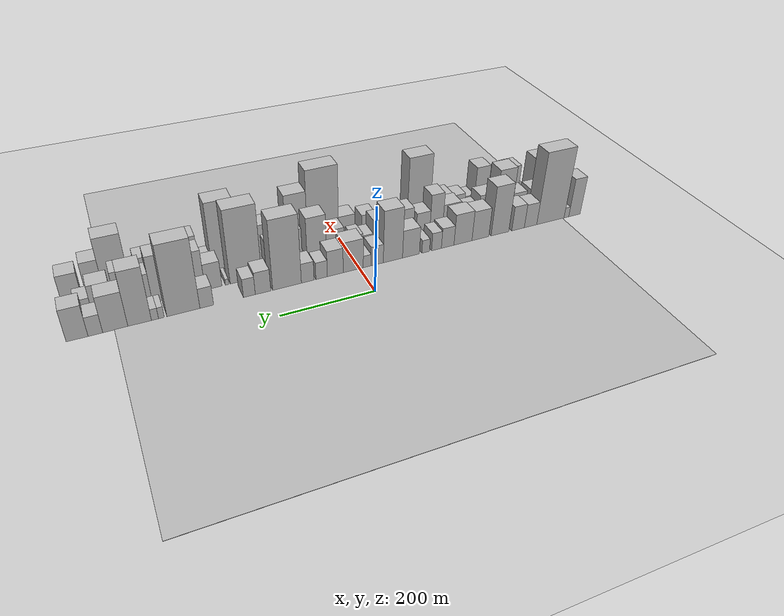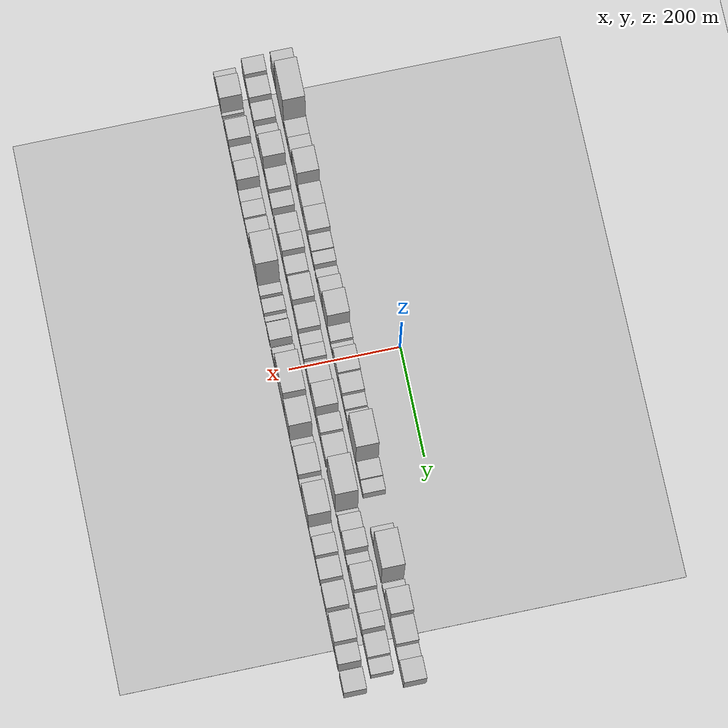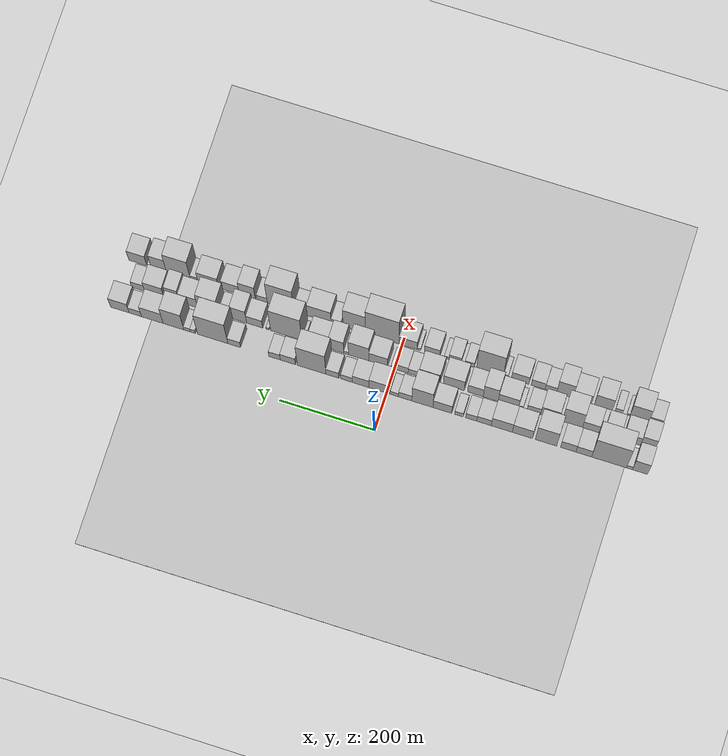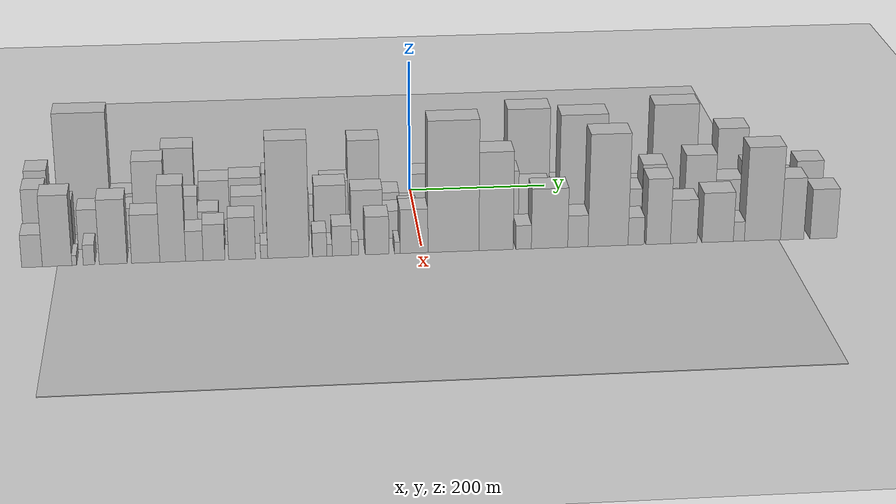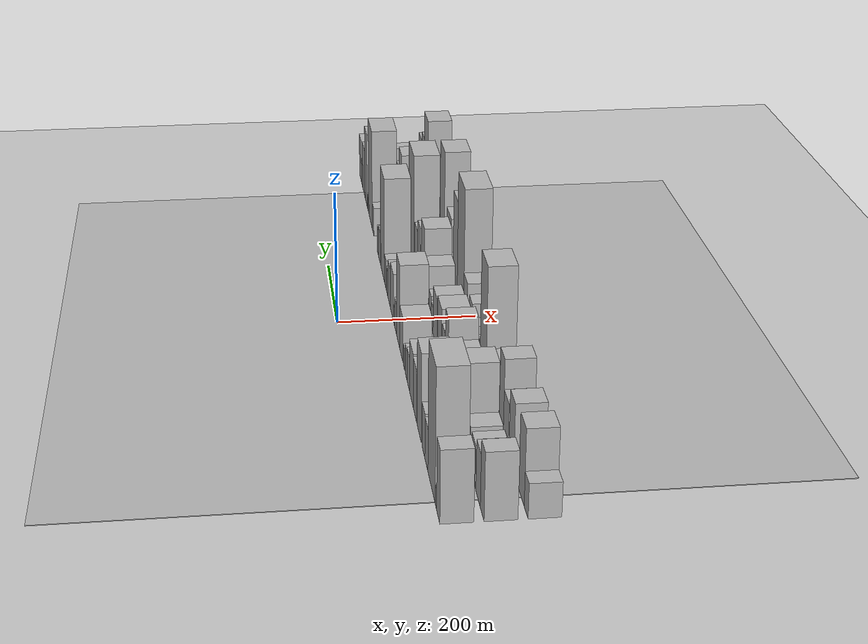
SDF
<?xml version="1.0" encoding="utf-8"?>

<sdf version="1.6">

   <world name="default">

      <gui fullscreen="0">

         <camera name="user_camera">

            <pose>-15 0 4.57585 0 0 0</pose>

            <view_controller>orbit</view_controller>

         </camera>

      </gui>

      <scene>

         <sky>

           <clouds>

             <speed>12</speed>

           </clouds>

         </sky>

         <ambient>0.4 0.4 0.4 1</ambient>

         <background>0.7 0.7 0.7 1</background>

         <shadows>1</shadows>

      </scene>

      <gravity>0 0 -9.8066</gravity>

      <magnetic_field>6e-06 2.3e-05 -4.2e-05</magnetic_field>

      <physics default="0" name="default_physics" type="ode">

         <ode>

            <solver>

               <type>quick</type>

               <iters>10</iters>

               <sor>1.0</sor>

               <use_dynamic_moi_rescaling>0</use_dynamic_moi_rescaling>

            </solver>

            <constraints>

               <cfm>0</cfm>

               <erp>0.2</erp>

               <contact_max_correcting_vel>100</contact_max_correcting_vel>

               <contact_surface_layer>0.001</contact_surface_layer>

            </constraints>

         </ode>

         <max_step_size>0.004</max_step_size>

         <real_time_factor>1</real_time_factor>

         <real_time_update_rate>250</real_time_update_rate>

      </physics>

      <light name="sun" type="directional">

         <cast_shadows>1</cast_shadows>

         <pose>0 0 10 0 0 0</pose>

         <diffuse>0.8 0.8 0.8 1</diffuse>

         <specular>0.2 0.2 0.2 1</specular>

         <attenuation>

            <range>1000</range>

            <constant>0.9</constant>

            <linear>0.01</linear>

            <quadratic>0.001</quadratic>

         </attenuation>

         <direction>-0.5 0.1 -0.9</direction>

      </light>

      <include>

         <name>ground_plane_1</name>

         <uri>model://HANNAS_ground_plane</uri>

         <pose>0 0 0  0 0 0</pose>

      </include>

      <include>

         <name>ground_plane_2</name>

         <uri>model://HANNAS_ground_plane</uri>

         <pose>100 0 0  0 0 0</pose>

      </include>

      <model name="building_1">

         <static>1</static>

         <pose frame="">100.0000 -532.3736 0 0.000000 0.000000 0.000000</pose>

         <link name="link">

            <pose frame="">0 0 49.50 0 0 0</pose>

            <collision name="collision">

               <geometry>

                  <box>

                     <size>40.0000 31.2527 99.0000</size>

                  </box>

               </geometry>

               <max_contacts>10</max_contacts>

               <surface>

                  <contact>

                     <ode/>

                  </contact>

                  <bounce/>

                  <friction>

                     <torsional>

                        <ode/>

                     </torsional>

                     <ode/>

                  </friction>

               </surface>

            </collision>

            <visual name="visual">

               <cast_shadows>0</cast_shadows>

               <geometry>

                  <box>

                     <size>40.0000 31.2527 99.0000</size>

                  </box>

               </geometry>

               <material>

                  <script>

                     <uri>model://HANNAS_wall/materials/scripts</uri>

                     <uri>model://HANNAS_wall/materials/textures</uri>

                     <name>vrc/HANNAS_wall</name>

                  </script>

               </material>

            </visual>

            <self_collide>0</self_collide>

            <enable_wind>0</enable_wind>

            <kinematic>0</kinematic>

         </link>

      </model>

      <model name="building_2">

         <static>1</static>

         <pose frame="">100.0000 -510.3500 0 0.000000 0.000000 0.000000</pose>

         <link name="link">

            <pose frame="">0 0 13.50 0 0 0</pose>

            <collision name="collision">

               <geometry>

                  <box>

                     <size>40.0000 12.7945 27.0000</size>

                  </box>

               </geometry>

               <max_contacts>10</max_contacts>

               <surface>

                  <contact>

                     <ode/>

                  </contact>

                  <bounce/>

                  <friction>

                     <torsional>

                        <ode/>

                     </torsional>

                     <ode/>

                  </friction>

               </surface>

            </collision>

            <visual name="visual">

               <cast_shadows>0</cast_shadows>

               <geometry>

                  <box>

                     <size>40.0000 12.7945 27.0000</size>

                  </box>

               </geometry>

               <material>

                  <script>

                     <uri>model://HANNAS_wall/materials/scripts</uri>

                     <uri>model://HANNAS_wall/materials/textures</uri>

                     <name>vrc/HANNAS_wall</name>

                  </script>

               </material>

            </visual>

            <self_collide>0</self_collide>

            <enable_wind>0</enable_wind>

            <kinematic>0</kinematic>

         </link>

      </model>

      <model name="building_3">

         <static>1</static>

         <pose frame="">100.0000 -467.4651 0 0.000000 0.000000 0.000000</pose>

         <link name="link">

            <pose frame="">0 0 91.50 0 0 0</pose>

            <collision name="collision">

               <geometry>

                  <box>

                     <size>40.0000 72.9752 183.0000</size>

                  </box>

               </geometry>

               <max_contacts>10</max_contacts>

               <surface>

                  <contact>

                     <ode/>

                  </contact>

                  <bounce/>

                  <friction>

                     <torsional>

                        <ode/>

                     </torsional>

                     <ode/>

                  </friction>

               </surface>

            </collision>

            <visual name="visual">

               <cast_shadows>0</cast_shadows>

               <geometry>

                  <box>

                     <size>40.0000 72.9752 183.0000</size>

                  </box>

               </geometry>

               <material>

                  <script>

                     <uri>model://HANNAS_wall/materials/scripts</uri>

                     <uri>model://HANNAS_wall/materials/textures</uri>

                     <name>vrc/HANNAS_wall</name>

                  </script>

               </material>

            </visual>

            <self_collide>0</self_collide>

            <enable_wind>0</enable_wind>

            <kinematic>0</kinematic>

         </link>

      </model>

      <model name="building_4">

         <static>1</static>

         <pose frame="">100.0000 -414.6393 0 0.000000 0.000000 0.000000</pose>

         <link name="link">

            <pose frame="">0 0 30.00 0 0 0</pose>

            <collision name="collision">

               <geometry>

                  <box>

                     <size>40.0000 32.6765 60.0000</size>

                  </box>

               </geometry>

               <max_contacts>10</max_contacts>

               <surface>

                  <contact>

                     <ode/>

                  </contact>

                  <bounce/>

                  <friction>

                     <torsional>

                        <ode/>

                     </torsional>

                     <ode/>

                  </friction>

               </surface>

            </collision>

            <visual name="visual">

               <cast_shadows>0</cast_shadows>

               <geometry>

                  <box>

                     <size>40.0000 32.6765 60.0000</size>

                  </box>

               </geometry>

               <material>

                  <script>

                     <uri>model://HANNAS_wall/materials/scripts</uri>

                     <uri>model://HANNAS_wall/materials/textures</uri>

                     <name>vrc/HANNAS_wall</name>

                  </script>

               </material>

            </visual>

            <self_collide>0</self_collide>

            <enable_wind>0</enable_wind>

            <kinematic>0</kinematic>

         </link>

      </model>

      <model name="building_5">

         <static>1</static>

         <pose frame="">100.0000 -382.0855 0 0.000000 0.000000 0.000000</pose>

         <link name="link">

            <pose frame="">0 0 31.50 0 0 0</pose>

            <collision name="collision">

               <geometry>

                  <box>

                     <size>40.0000 32.4310 63.0000</size>

                  </box>

               </geometry>

               <max_contacts>10</max_contacts>

               <surface>

                  <contact>

                     <ode/>

                  </contact>

                  <bounce/>

                  <friction>

                     <torsional>

                        <ode/>

                     </torsional>

                     <ode/>

                  </friction>

               </surface>

            </collision>

            <visual name="visual">

               <cast_shadows>0</cast_shadows>

               <geometry>

                  <box>

                     <size>40.0000 32.4310 63.0000</size>

                  </box>

               </geometry>

               <material>

                  <script>

                     <uri>model://HANNAS_wall/materials/scripts</uri>

                     <uri>model://HANNAS_wall/materials/textures</uri>

                     <name>vrc/HANNAS_wall</name>

                  </script>

               </material>

            </visual>

            <self_collide>0</self_collide>

            <enable_wind>0</enable_wind>

            <kinematic>0</kinematic>

         </link>

      </model>

      <model name="building_6">

         <static>1</static>

         <pose frame="">100.0000 -335.4556 0 0.000000 0.000000 0.000000</pose>

         <link name="link">

            <pose frame="">0 0 63.00 0 0 0</pose>

            <collision name="collision">

               <geometry>

                  <box>

                     <size>40.0000 44.8287 126.0000</size>

                  </box>

               </geometry>

               <max_contacts>10</max_contacts>

               <surface>

                  <contact>

                     <ode/>

                  </contact>

                  <bounce/>

                  <friction>

                     <torsional>

                        <ode/>

                     </torsional>

                     <ode/>

                  </friction>

               </surface>

            </collision>

            <visual name="visual">

               <cast_shadows>0</cast_shadows>

               <geometry>

                  <box>

                     <size>40.0000 44.8287 126.0000</size>

                  </box>

               </geometry>

               <material>

                  <script>

                     <uri>model://HANNAS_wall/materials/scripts</uri>

                     <uri>model://HANNAS_wall/materials/textures</uri>

                     <name>vrc/HANNAS_wall</name>

                  </script>

               </material>

            </visual>

            <self_collide>0</self_collide>

            <enable_wind>0</enable_wind>

            <kinematic>0</kinematic>

         </link>

      </model>

      <model name="building_7">

         <static>1</static>

         <pose frame="">100.0000 -285.9318 0 0.000000 0.000000 0.000000</pose>

         <link name="link">

            <pose frame="">0 0 37.50 0 0 0</pose>

            <collision name="collision">

               <geometry>

                  <box>

                     <size>40.0000 42.2188 75.0000</size>

                  </box>

               </geometry>

               <max_contacts>10</max_contacts>

               <surface>

                  <contact>

                     <ode/>

                  </contact>

                  <bounce/>

                  <friction>

                     <torsional>

                        <ode/>

                     </torsional>

                     <ode/>

                  </friction>

               </surface>

            </collision>

            <visual name="visual">

               <cast_shadows>0</cast_shadows>

               <geometry>

                  <box>

                     <size>40.0000 42.2188 75.0000</size>

                  </box>

               </geometry>

               <material>

                  <script>

                     <uri>model://HANNAS_wall/materials/scripts</uri>

                     <uri>model://HANNAS_wall/materials/textures</uri>

                     <name>vrc/HANNAS_wall</name>

                  </script>

               </material>

            </visual>

            <self_collide>0</self_collide>

            <enable_wind>0</enable_wind>

            <kinematic>0</kinematic>

         </link>

      </model>

      <model name="building_8">

         <static>1</static>

         <pose frame="">100.0000 -242.5568 0 0.000000 0.000000 0.000000</pose>

         <link name="link">

            <pose frame="">0 0 39.00 0 0 0</pose>

            <collision name="collision">

               <geometry>

                  <box>

                     <size>40.0000 44.5313 78.0000</size>

                  </box>

               </geometry>

               <max_contacts>10</max_contacts>

               <surface>

                  <contact>

                     <ode/>

                  </contact>

                  <bounce/>

                  <friction>

                     <torsional>

                        <ode/>

                     </torsional>

                     <ode/>

                  </friction>

               </surface>

            </collision>

            <visual name="visual">

               <cast_shadows>0</cast_shadows>

               <geometry>

                  <box>

                     <size>40.0000 44.5313 78.0000</size>

                  </box>

               </geometry>

               <material>

                  <script>

                     <uri>model://HANNAS_wall/materials/scripts</uri>

                     <uri>model://HANNAS_wall/materials/textures</uri>

                     <name>vrc/HANNAS_wall</name>

                  </script>

               </material>

            </visual>

            <self_collide>0</self_collide>

            <enable_wind>0</enable_wind>

            <kinematic>0</kinematic>

         </link>

      </model>

      <model name="building_9">

         <static>1</static>

         <pose frame="">100.0000 -205.0345 0 0.000000 0.000000 0.000000</pose>

         <link name="link">

            <pose frame="">0 0 25.50 0 0 0</pose>

            <collision name="collision">

               <geometry>

                  <box>

                     <size>40.0000 30.5132 51.0000</size>

                  </box>

               </geometry>

               <max_contacts>10</max_contacts>

               <surface>

                  <contact>

                     <ode/>

                  </contact>

                  <bounce/>

                  <friction>

                     <torsional>

                        <ode/>

                     </torsional>

                     <ode/>

                  </friction>

               </surface>

            </collision>

            <visual name="visual">

               <cast_shadows>0</cast_shadows>

               <geometry>

                  <box>

                     <size>40.0000 30.5132 51.0000</size>

                  </box>

               </geometry>

               <material>

                  <script>

                     <uri>model://HANNAS_wall/materials/scripts</uri>

                     <uri>model://HANNAS_wall/materials/textures</uri>

                     <name>vrc/HANNAS_wall</name>

                  </script>

               </material>

            </visual>

            <self_collide>0</self_collide>

            <enable_wind>0</enable_wind>

            <kinematic>0</kinematic>

         </link>

      </model>

      <model name="building_10">

         <static>1</static>

         <pose frame="">100.0000 -178.0144 0 0.000000 0.000000 0.000000</pose>

         <link name="link">

            <pose frame="">0 0 22.50 0 0 0</pose>

            <collision name="collision">

               <geometry>

                  <box>

                     <size>40.0000 23.5270 45.0000</size>

                  </box>

               </geometry>

               <max_contacts>10</max_contacts>

               <surface>

                  <contact>

                     <ode/>

                  </contact>

                  <bounce/>

                  <friction>

                     <torsional>

                        <ode/>

                     </torsional>

                     <ode/>

                  </friction>

               </surface>

            </collision>

            <visual name="visual">

               <cast_shadows>0</cast_shadows>

               <geometry>

                  <box>

                     <size>40.0000 23.5270 45.0000</size>

                  </box>

               </geometry>

               <material>

                  <script>

                     <uri>model://HANNAS_wall/materials/scripts</uri>

                     <uri>model://HANNAS_wall/materials/textures</uri>

                     <name>vrc/HANNAS_wall</name>

                  </script>

               </material>

            </visual>

            <self_collide>0</self_collide>

            <enable_wind>0</enable_wind>

            <kinematic>0</kinematic>

         </link>

      </model>

      <model name="building_11">

         <static>1</static>

         <pose frame="">100.0000 -152.1517 0 0.000000 0.000000 0.000000</pose>

         <link name="link">

            <pose frame="">0 0 16.50 0 0 0</pose>

            <collision name="collision">

               <geometry>

                  <box>

                     <size>40.0000 18.1985 33.0000</size>

                  </box>

               </geometry>

               <max_contacts>10</max_contacts>

               <surface>

                  <contact>

                     <ode/>

                  </contact>

                  <bounce/>

                  <friction>

                     <torsional>

                        <ode/>

                     </torsional>

                     <ode/>

                  </friction>

               </surface>

            </collision>

            <visual name="visual">

               <cast_shadows>0</cast_shadows>

               <geometry>

                  <box>

                     <size>40.0000 18.1985 33.0000</size>

                  </box>

               </geometry>

               <material>

                  <script>

                     <uri>model://HANNAS_wall/materials/scripts</uri>

                     <uri>model://HANNAS_wall/materials/textures</uri>

                     <name>vrc/HANNAS_wall</name>

                  </script>

               </material>

            </visual>

            <self_collide>0</self_collide>

            <enable_wind>0</enable_wind>

            <kinematic>0</kinematic>

         </link>

      </model>

      <model name="building_12">

         <static>1</static>

         <pose frame="">100.0000 -117.2215 0 0.000000 0.000000 0.000000</pose>

         <link name="link">

            <pose frame="">0 0 34.50 0 0 0</pose>

            <collision name="collision">

               <geometry>

                  <box>

                     <size>40.0000 39.6619 69.0000</size>

                  </box>

               </geometry>

               <max_contacts>10</max_contacts>

               <surface>

                  <contact>

                     <ode/>

                  </contact>

                  <bounce/>

                  <friction>

                     <torsional>

                        <ode/>

                     </torsional>

                     <ode/>

                  </friction>

               </surface>

            </collision>

            <visual name="visual">

               <cast_shadows>0</cast_shadows>

               <geometry>

                  <box>

                     <size>40.0000 39.6619 69.0000</size>

                  </box>

               </geometry>

               <material>

                  <script>

                     <uri>model://HANNAS_wall/materials/scripts</uri>

                     <uri>model://HANNAS_wall/materials/textures</uri>

                     <name>vrc/HANNAS_wall</name>

                  </script>

               </material>

            </visual>

            <self_collide>0</self_collide>

            <enable_wind>0</enable_wind>

            <kinematic>0</kinematic>

         </link>

      </model>

      <model name="building_13">

         <static>1</static>

         <pose frame="">100.0000 -75.1150 0 0.000000 0.000000 0.000000</pose>

         <link name="link">

            <pose frame="">0 0 64.50 0 0 0</pose>

            <collision name="collision">

               <geometry>

                  <box>

                     <size>40.0000 44.5510 129.0000</size>

                  </box>

               </geometry>

               <max_contacts>10</max_contacts>

               <surface>

                  <contact>

                     <ode/>

                  </contact>

                  <bounce/>

                  <friction>

                     <torsional>

                        <ode/>

                     </torsional>

                     <ode/>

                  </friction>

               </surface>

            </collision>

            <visual name="visual">

               <cast_shadows>0</cast_shadows>

               <geometry>

                  <box>

                     <size>40.0000 44.5510 129.0000</size>

                  </box>

               </geometry>

               <material>

                  <script>

                     <uri>model://HANNAS_wall/materials/scripts</uri>

                     <uri>model://HANNAS_wall/materials/textures</uri>

                     <name>vrc/HANNAS_wall</name>

                  </script>

               </material>

            </visual>

            <self_collide>0</self_collide>

            <enable_wind>0</enable_wind>

            <kinematic>0</kinematic>

         </link>

      </model>

      <model name="building_14">

         <static>1</static>

         <pose frame="">100.0000 -38.8393 0 0.000000 0.000000 0.000000</pose>

         <link name="link">

            <pose frame="">0 0 24.00 0 0 0</pose>

            <collision name="collision">

               <geometry>

                  <box>

                     <size>40.0000 28.0004 48.0000</size>

                  </box>

               </geometry>

               <max_contacts>10</max_contacts>

               <surface>

                  <contact>

                     <ode/>

                  </contact>

                  <bounce/>

                  <friction>

                     <torsional>

                        <ode/>

                     </torsional>

                     <ode/>

                  </friction>

               </surface>

            </collision>

            <visual name="visual">

               <cast_shadows>0</cast_shadows>

               <geometry>

                  <box>

                     <size>40.0000 28.0004 48.0000</size>

                  </box>

               </geometry>

               <material>

                  <script>

                     <uri>model://HANNAS_wall/materials/scripts</uri>

                     <uri>model://HANNAS_wall/materials/textures</uri>

                     <name>vrc/HANNAS_wall</name>

                  </script>

               </material>

            </visual>

            <self_collide>0</self_collide>

            <enable_wind>0</enable_wind>

            <kinematic>0</kinematic>

         </link>

      </model>

      <model name="building_15">

         <static>1</static>

         <pose frame="">100.0000 -16.0069 0 0.000000 0.000000 0.000000</pose>

         <link name="link">

            <pose frame="">0 0 15.00 0 0 0</pose>

            <collision name="collision">

               <geometry>

                  <box>

                     <size>40.0000 17.6644 30.0000</size>

                  </box>

               </geometry>

               <max_contacts>10</max_contacts>

               <surface>

                  <contact>

                     <ode/>

                  </contact>

                  <bounce/>

                  <friction>

                     <torsional>

                        <ode/>

                     </torsional>

                     <ode/>

                  </friction>

               </surface>

            </collision>

            <visual name="visual">

               <cast_shadows>0</cast_shadows>

               <geometry>

                  <box>

                     <size>40.0000 17.6644 30.0000</size>

                  </box>

               </geometry>

               <material>

                  <script>

                     <uri>model://HANNAS_wall/materials/scripts</uri>

                     <uri>model://HANNAS_wall/materials/textures</uri>

                     <name>vrc/HANNAS_wall</name>

                  </script>

               </material>

            </visual>

            <self_collide>0</self_collide>

            <enable_wind>0</enable_wind>

            <kinematic>0</kinematic>

         </link>

      </model>

      <model name="building_16">

         <static>1</static>

         <pose frame="">100.0000 15.2583 0 0.000000 0.000000 0.000000</pose>

         <link name="link">

            <pose frame="">0 0 37.50 0 0 0</pose>

            <collision name="collision">

               <geometry>

                  <box>

                     <size>40.0000 44.8660 75.0000</size>

                  </box>

               </geometry>

               <max_contacts>10</max_contacts>

               <surface>

                  <contact>

                     <ode/>

                  </contact>

                  <bounce/>

                  <friction>

                     <torsional>

                        <ode/>

                     </torsional>

                     <ode/>

                  </friction>

               </surface>

            </collision>

            <visual name="visual">

               <cast_shadows>0</cast_shadows>

               <geometry>

                  <box>

                     <size>40.0000 44.8660 75.0000</size>

                  </box>

               </geometry>

               <material>

                  <script>

                     <uri>model://HANNAS_wall/materials/scripts</uri>

                     <uri>model://HANNAS_wall/materials/textures</uri>

                     <name>vrc/HANNAS_wall</name>

                  </script>

               </material>

            </visual>

            <self_collide>0</self_collide>

            <enable_wind>0</enable_wind>

            <kinematic>0</kinematic>

         </link>

      </model>

      <model name="building_17">

         <static>1</static>

         <pose frame="">100.0000 55.1957 0 0.000000 0.000000 0.000000</pose>

         <link name="link">

            <pose frame="">0 0 31.50 0 0 0</pose>

            <collision name="collision">

               <geometry>

                  <box>

                     <size>40.0000 35.0089 63.0000</size>

                  </box>

               </geometry>

               <max_contacts>10</max_contacts>

               <surface>

                  <contact>

                     <ode/>

                  </contact>

                  <bounce/>

                  <friction>

                     <torsional>

                        <ode/>

                     </torsional>

                     <ode/>

                  </friction>

               </surface>

            </collision>

            <visual name="visual">

               <cast_shadows>0</cast_shadows>

               <geometry>

                  <box>

                     <size>40.0000 35.0089 63.0000</size>

                  </box>

               </geometry>

               <material>

                  <script>

                     <uri>model://HANNAS_wall/materials/scripts</uri>

                     <uri>model://HANNAS_wall/materials/textures</uri>

                     <name>vrc/HANNAS_wall</name>

                  </script>

               </material>

            </visual>

            <self_collide>0</self_collide>

            <enable_wind>0</enable_wind>

            <kinematic>0</kinematic>

         </link>

      </model>

      <model name="building_18">

         <static>1</static>

         <pose frame="">100.0000 85.0959 0 0.000000 0.000000 0.000000</pose>

         <link name="link">

            <pose frame="">0 0 21.00 0 0 0</pose>

            <collision name="collision">

               <geometry>

                  <box>

                     <size>40.0000 24.7916 42.0000</size>

                  </box>

               </geometry>

               <max_contacts>10</max_contacts>

               <surface>

                  <contact>

                     <ode/>

                  </contact>

                  <bounce/>

                  <friction>

                     <torsional>

                        <ode/>

                     </torsional>

                     <ode/>

                  </friction>

               </surface>

            </collision>

            <visual name="visual">

               <cast_shadows>0</cast_shadows>

               <geometry>

                  <box>

                     <size>40.0000 24.7916 42.0000</size>

                  </box>

               </geometry>

               <material>

                  <script>

                     <uri>model://HANNAS_wall/materials/scripts</uri>

                     <uri>model://HANNAS_wall/materials/textures</uri>

                     <name>vrc/HANNAS_wall</name>

                  </script>

               </material>

            </visual>

            <self_collide>0</self_collide>

            <enable_wind>0</enable_wind>

            <kinematic>0</kinematic>

         </link>

      </model>

      <model name="building_19">

         <static>1</static>

         <pose frame="">100.0000 115.1300 0 0.000000 0.000000 0.000000</pose>

         <link name="link">

            <pose frame="">0 0 24.00 0 0 0</pose>

            <collision name="collision">

               <geometry>

                  <box>

                     <size>40.0000 27.2765 48.0000</size>

                  </box>

               </geometry>

               <max_contacts>10</max_contacts>

               <surface>

                  <contact>

                     <ode/>

                  </contact>

                  <bounce/>

                  <friction>

                     <torsional>

                        <ode/>

                     </torsional>

                     <ode/>

                  </friction>

               </surface>

            </collision>

            <visual name="visual">

               <cast_shadows>0</cast_shadows>

               <geometry>

                  <box>

                     <size>40.0000 27.2765 48.0000</size>

                  </box>

               </geometry>

               <material>

                  <script>

                     <uri>model://HANNAS_wall/materials/scripts</uri>

                     <uri>model://HANNAS_wall/materials/textures</uri>

                     <name>vrc/HANNAS_wall</name>

                  </script>

               </material>

            </visual>

            <self_collide>0</self_collide>

            <enable_wind>0</enable_wind>

            <kinematic>0</kinematic>

         </link>

      </model>

      <model name="building_20">

         <static>1</static>

         <pose frame="">100.0000 159.0901 0 0.000000 0.000000 0.000000</pose>

         <link name="link">

            <pose frame="">0 0 84.00 0 0 0</pose>

            <collision name="collision">

               <geometry>

                  <box>

                     <size>40.0000 60.6438 168.0000</size>

                  </box>

               </geometry>

               <max_contacts>10</max_contacts>

               <surface>

                  <contact>

                     <ode/>

                  </contact>

                  <bounce/>

                  <friction>

                     <torsional>

                        <ode/>

                     </torsional>

                     <ode/>

                  </friction>

               </surface>

            </collision>

            <visual name="visual">

               <cast_shadows>0</cast_shadows>

               <geometry>

                  <box>

                     <size>40.0000 60.6438 168.0000</size>

                  </box>

               </geometry>

               <material>

                  <script>

                     <uri>model://HANNAS_wall/materials/scripts</uri>

                     <uri>model://HANNAS_wall/materials/textures</uri>

                     <name>vrc/HANNAS_wall</name>

                  </script>

               </material>

            </visual>

            <self_collide>0</self_collide>

            <enable_wind>0</enable_wind>

            <kinematic>0</kinematic>

         </link>

      </model>

      <model name="building_21">

         <static>1</static>

         <pose frame="">100.0000 209.4794 0 0.000000 0.000000 0.000000</pose>

         <link name="link">

            <pose frame="">0 0 27.00 0 0 0</pose>

            <collision name="collision">

               <geometry>

                  <box>

                     <size>40.0000 32.1349 54.0000</size>

                  </box>

               </geometry>

               <max_contacts>10</max_contacts>

               <surface>

                  <contact>

                     <ode/>

                  </contact>

                  <bounce/>

                  <friction>

                     <torsional>

                        <ode/>

                     </torsional>

                     <ode/>

                  </friction>

               </surface>

            </collision>

            <visual name="visual">

               <cast_shadows>0</cast_shadows>

               <geometry>

                  <box>

                     <size>40.0000 32.1349 54.0000</size>

                  </box>

               </geometry>

               <material>

                  <script>

                     <uri>model://HANNAS_wall/materials/scripts</uri>

                     <uri>model://HANNAS_wall/materials/textures</uri>

                     <name>vrc/HANNAS_wall</name>

                  </script>

               </material>

            </visual>

            <self_collide>0</self_collide>

            <enable_wind>0</enable_wind>

            <kinematic>0</kinematic>

         </link>

      </model>

      <model name="building_22">

         <static>1</static>

         <pose frame="">100.0000 237.7164 0 0.000000 0.000000 0.000000</pose>

         <link name="link">

            <pose frame="">0 0 22.50 0 0 0</pose>

            <collision name="collision">

               <geometry>

                  <box>

                     <size>40.0000 24.3390 45.0000</size>

                  </box>

               </geometry>

               <max_contacts>10</max_contacts>

               <surface>

                  <contact>

                     <ode/>

                  </contact>

                  <bounce/>

                  <friction>

                     <torsional>

                        <ode/>

                     </torsional>

                     <ode/>

                  </friction>

               </surface>

            </collision>

            <visual name="visual">

               <cast_shadows>0</cast_shadows>

               <geometry>

                  <box>

                     <size>40.0000 24.3390 45.0000</size>

                  </box>

               </geometry>

               <material>

                  <script>

                     <uri>model://HANNAS_wall/materials/scripts</uri>

                     <uri>model://HANNAS_wall/materials/textures</uri>

                     <name>vrc/HANNAS_wall</name>

                  </script>

               </material>

            </visual>

            <self_collide>0</self_collide>

            <enable_wind>0</enable_wind>

            <kinematic>0</kinematic>

         </link>

      </model>

      <model name="building_23">

         <static>1</static>

         <pose frame="">100.0000 323.4313 0 0.000000 0.000000 0.000000</pose>

         <link name="link">

            <pose frame="">0 0 24.00 0 0 0</pose>

            <collision name="collision">

               <geometry>

                  <box>

                     <size>40.0000 27.0303 48.0000</size>

                  </box>

               </geometry>

               <max_contacts>10</max_contacts>

               <surface>

                  <contact>

                     <ode/>

                  </contact>

                  <bounce/>

                  <friction>

                     <torsional>

                        <ode/>

                     </torsional>

                     <ode/>

                  </friction>

               </surface>

            </collision>

            <visual name="visual">

               <cast_shadows>0</cast_shadows>

               <geometry>

                  <box>

                     <size>40.0000 27.0303 48.0000</size>

                  </box>

               </geometry>

               <material>

                  <script>

                     <uri>model://HANNAS_wall/materials/scripts</uri>

                     <uri>model://HANNAS_wall/materials/textures</uri>

                     <name>vrc/HANNAS_wall</name>

                  </script>

               </material>

            </visual>

            <self_collide>0</self_collide>

            <enable_wind>0</enable_wind>

            <kinematic>0</kinematic>

         </link>

      </model>

      <model name="building_24">

         <static>1</static>

         <pose frame="">100.0000 369.1194 0 0.000000 0.000000 0.000000</pose>

         <link name="link">

            <pose frame="">0 0 84.00 0 0 0</pose>

            <collision name="collision">

               <geometry>

                  <box>

                     <size>40.0000 64.3458 168.0000</size>

                  </box>

               </geometry>

               <max_contacts>10</max_contacts>

               <surface>

                  <contact>

                     <ode/>

                  </contact>

                  <bounce/>

                  <friction>

                     <torsional>

                        <ode/>

                     </torsional>

                     <ode/>

                  </friction>

               </surface>

            </collision>

            <visual name="visual">

               <cast_shadows>0</cast_shadows>

               <geometry>

                  <box>

                     <size>40.0000 64.3458 168.0000</size>

                  </box>

               </geometry>

               <material>

                  <script>

                     <uri>model://HANNAS_wall/materials/scripts</uri>

                     <uri>model://HANNAS_wall/materials/textures</uri>

                     <name>vrc/HANNAS_wall</name>

                  </script>

               </material>

            </visual>

            <self_collide>0</self_collide>

            <enable_wind>0</enable_wind>

            <kinematic>0</kinematic>

         </link>

      </model>

      <model name="building_25">

         <static>1</static>

         <pose frame="">100.0000 411.7734 0 0.000000 0.000000 0.000000</pose>

         <link name="link">

            <pose frame="">0 0 13.50 0 0 0</pose>

            <collision name="collision">

               <geometry>

                  <box>

                     <size>40.0000 10.9621 27.0000</size>

                  </box>

               </geometry>

               <max_contacts>10</max_contacts>

               <surface>

                  <contact>

                     <ode/>

                  </contact>

                  <bounce/>

                  <friction>

                     <torsional>

                        <ode/>

                     </torsional>

                     <ode/>

                  </friction>

               </surface>

            </collision>

            <visual name="visual">

               <cast_shadows>0</cast_shadows>

               <geometry>

                  <box>

                     <size>40.0000 10.9621 27.0000</size>

                  </box>

               </geometry>

               <material>

                  <script>

                     <uri>model://HANNAS_wall/materials/scripts</uri>

                     <uri>model://HANNAS_wall/materials/textures</uri>

                     <name>vrc/HANNAS_wall</name>

                  </script>

               </material>

            </visual>

            <self_collide>0</self_collide>

            <enable_wind>0</enable_wind>

            <kinematic>0</kinematic>

         </link>

      </model>

      <model name="building_26">

         <static>1</static>

         <pose frame="">100.0000 423.9517 0 0.000000 0.000000 0.000000</pose>

         <link name="link">

            <pose frame="">0 0 13.50 0 0 0</pose>

            <collision name="collision">

               <geometry>

                  <box>

                     <size>40.0000 13.3947 27.0000</size>

                  </box>

               </geometry>

               <max_contacts>10</max_contacts>

               <surface>

                  <contact>

                     <ode/>

                  </contact>

                  <bounce/>

                  <friction>

                     <torsional>

                        <ode/>

                     </torsional>

                     <ode/>

                  </friction>

               </surface>

            </collision>

            <visual name="visual">

               <cast_shadows>0</cast_shadows>

               <geometry>

                  <box>

                     <size>40.0000 13.3947 27.0000</size>

                  </box>

               </geometry>

               <material>

                  <script>

                     <uri>model://HANNAS_wall/materials/scripts</uri>

                     <uri>model://HANNAS_wall/materials/textures</uri>

                     <name>vrc/HANNAS_wall</name>

                  </script>

               </material>

            </visual>

            <self_collide>0</self_collide>

            <enable_wind>0</enable_wind>

            <kinematic>0</kinematic>

         </link>

      </model>

      <model name="building_27">

         <static>1</static>

         <pose frame="">100.0000 452.7484 0 0.000000 0.000000 0.000000</pose>

         <link name="link">

            <pose frame="">0 0 64.50 0 0 0</pose>

            <collision name="collision">

               <geometry>

                  <box>

                     <size>40.0000 44.1987 129.0000</size>

                  </box>

               </geometry>

               <max_contacts>10</max_contacts>

               <surface>

                  <contact>

                     <ode/>

                  </contact>

                  <bounce/>

                  <friction>

                     <torsional>

                        <ode/>

                     </torsional>

                     <ode/>

                  </friction>

               </surface>

            </collision>

            <visual name="visual">

               <cast_shadows>0</cast_shadows>

               <geometry>

                  <box>

                     <size>40.0000 44.1987 129.0000</size>

                  </box>

               </geometry>

               <material>

                  <script>

                     <uri>model://HANNAS_wall/materials/scripts</uri>

                     <uri>model://HANNAS_wall/materials/textures</uri>

                     <name>vrc/HANNAS_wall</name>

                  </script>

               </material>

            </visual>

            <self_collide>0</self_collide>

            <enable_wind>0</enable_wind>

            <kinematic>0</kinematic>

         </link>

      </model>

      <model name="building_28">

         <static>1</static>

         <pose frame="">100.0000 498.0288 0 0.000000 0.000000 0.000000</pose>

         <link name="link">

            <pose frame="">0 0 42.00 0 0 0</pose>

            <collision name="collision">

               <geometry>

                  <box>

                     <size>40.0000 46.3619 84.0000</size>

                  </box>

               </geometry>

               <max_contacts>10</max_contacts>

               <surface>

                  <contact>

                     <ode/>

                  </contact>

                  <bounce/>

                  <friction>

                     <torsional>

                        <ode/>

                     </torsional>

                     <ode/>

                  </friction>

               </surface>

            </collision>

            <visual name="visual">

               <cast_shadows>0</cast_shadows>

               <geometry>

                  <box>

                     <size>40.0000 46.3619 84.0000</size>

                  </box>

               </geometry>

               <material>

                  <script>

                     <uri>model://HANNAS_wall/materials/scripts</uri>

                     <uri>model://HANNAS_wall/materials/textures</uri>

                     <name>vrc/HANNAS_wall</name>

                  </script>

               </material>

            </visual>

            <self_collide>0</self_collide>

            <enable_wind>0</enable_wind>

            <kinematic>0</kinematic>

         </link>

      </model>

      <model name="building_29">

         <static>1</static>

         <pose frame="">100.0000 534.4678 0 0.000000 0.000000 0.000000</pose>

         <link name="link">

            <pose frame="">0 0 22.50 0 0 0</pose>

            <collision name="collision">

               <geometry>

                  <box>

                     <size>40.0000 26.5162 45.0000</size>

                  </box>

               </geometry>

               <max_contacts>10</max_contacts>

               <surface>

                  <contact>

                     <ode/>

                  </contact>

                  <bounce/>

                  <friction>

                     <torsional>

                        <ode/>

                     </torsional>

                     <ode/>

                  </friction>

               </surface>

            </collision>

            <visual name="visual">

               <cast_shadows>0</cast_shadows>

               <geometry>

                  <box>

                     <size>40.0000 26.5162 45.0000</size>

                  </box>

               </geometry>

               <material>

                  <script>

                     <uri>model://HANNAS_wall/materials/scripts</uri>

                     <uri>model://HANNAS_wall/materials/textures</uri>

                     <name>vrc/HANNAS_wall</name>

                  </script>

               </material>

            </visual>

            <self_collide>0</self_collide>

            <enable_wind>0</enable_wind>

            <kinematic>0</kinematic>

         </link>

      </model>

      <model name="building_30">

         <static>1</static>

         <pose frame="">100.0000 567.3523 0 0.000000 0.000000 0.000000</pose>

         <link name="link">

            <pose frame="">0 0 37.50 0 0 0</pose>

            <collision name="collision">

               <geometry>

                  <box>

                     <size>40.0000 39.2528 75.0000</size>

                  </box>

               </geometry>

               <max_contacts>10</max_contacts>

               <surface>

                  <contact>

                     <ode/>

                  </contact>

                  <bounce/>

                  <friction>

                     <torsional>

                        <ode/>

                     </torsional>

                     <ode/>

                  </friction>

               </surface>

            </collision>

            <visual name="visual">

               <cast_shadows>0</cast_shadows>

               <geometry>

                  <box>

                     <size>40.0000 39.2528 75.0000</size>

                  </box>

               </geometry>

               <material>

                  <script>

                     <uri>model://HANNAS_wall/materials/scripts</uri>

                     <uri>model://HANNAS_wall/materials/textures</uri>

                     <name>vrc/HANNAS_wall</name>

                  </script>

               </material>

            </visual>

            <self_collide>0</self_collide>

            <enable_wind>0</enable_wind>

            <kinematic>0</kinematic>

         </link>

      </model>

      <model name="building_31">

         <static>1</static>

         <pose frame="">152.0000 -532.7235 0 0.000000 0.000000 0.000000</pose>

         <link name="link">

            <pose frame="">0 0 46.50 0 0 0</pose>

            <collision name="collision">

               <geometry>

                  <box>

                     <size>40.0000 30.5529 93.0000</size>

                  </box>

               </geometry>

               <max_contacts>10</max_contacts>

               <surface>

                  <contact>

                     <ode/>

                  </contact>

                  <bounce/>

                  <friction>

                     <torsional>

                        <ode/>

                     </torsional>

                     <ode/>

                  </friction>

               </surface>

            </collision>

            <visual name="visual">

               <cast_shadows>0</cast_shadows>

               <geometry>

                  <box>

                     <size>40.0000 30.5529 93.0000</size>

                  </box>

               </geometry>

               <material>

                  <script>

                     <uri>model://HANNAS_wall/materials/scripts</uri>

                     <uri>model://HANNAS_wall/materials/textures</uri>

                     <name>vrc/HANNAS_wall</name>

                  </script>

               </material>

            </visual>

            <self_collide>0</self_collide>

            <enable_wind>0</enable_wind>

            <kinematic>0</kinematic>

         </link>

      </model>

      <model name="building_32">

         <static>1</static>

         <pose frame="">152.0000 -499.0057 0 0.000000 0.000000 0.000000</pose>

         <link name="link">

            <pose frame="">0 0 36.00 0 0 0</pose>

            <collision name="collision">

               <geometry>

                  <box>

                     <size>40.0000 36.8827 72.0000</size>

                  </box>

               </geometry>

               <max_contacts>10</max_contacts>

               <surface>

                  <contact>

                     <ode/>

                  </contact>

                  <bounce/>

                  <friction>

                     <torsional>

                        <ode/>

                     </torsional>

                     <ode/>

                  </friction>

               </surface>

            </collision>

            <visual name="visual">

               <cast_shadows>0</cast_shadows>

               <geometry>

                  <box>

                     <size>40.0000 36.8827 72.0000</size>

                  </box>

               </geometry>

               <material>

                  <script>

                     <uri>model://HANNAS_wall/materials/scripts</uri>

                     <uri>model://HANNAS_wall/materials/textures</uri>

                     <name>vrc/HANNAS_wall</name>

                  </script>

               </material>

            </visual>

            <self_collide>0</self_collide>

            <enable_wind>0</enable_wind>

            <kinematic>0</kinematic>

         </link>

      </model>

      <model name="building_33">

         <static>1</static>

         <pose frame="">152.0000 -457.7530 0 0.000000 0.000000 0.000000</pose>

         <link name="link">

            <pose frame="">0 0 30.00 0 0 0</pose>

            <collision name="collision">

               <geometry>

                  <box>

                     <size>40.0000 33.6228 60.0000</size>

                  </box>

               </geometry>

               <max_contacts>10</max_contacts>

               <surface>

                  <contact>

                     <ode/>

                  </contact>

                  <bounce/>

                  <friction>

                     <torsional>

                        <ode/>

                     </torsional>

                     <ode/>

                  </friction>

               </surface>

            </collision>

            <visual name="visual">

               <cast_shadows>0</cast_shadows>

               <geometry>

                  <box>

                     <size>40.0000 33.6228 60.0000</size>

                  </box>

               </geometry>

               <material>

                  <script>

                     <uri>model://HANNAS_wall/materials/scripts</uri>

                     <uri>model://HANNAS_wall/materials/textures</uri>

                     <name>vrc/HANNAS_wall</name>

                  </script>

               </material>

            </visual>

            <self_collide>0</self_collide>

            <enable_wind>0</enable_wind>

            <kinematic>0</kinematic>

         </link>

      </model>

      <model name="building_34">

         <static>1</static>

         <pose frame="">152.0000 -413.5753 0 0.000000 0.000000 0.000000</pose>

         <link name="link">

            <pose frame="">0 0 30.00 0 0 0</pose>

            <collision name="collision">

               <geometry>

                  <box>

                     <size>40.0000 34.7326 60.0000</size>

                  </box>

               </geometry>

               <max_contacts>10</max_contacts>

               <surface>

                  <contact>

                     <ode/>

                  </contact>

                  <bounce/>

                  <friction>

                     <torsional>

                        <ode/>

                     </torsional>

                     <ode/>

                  </friction>

               </surface>

            </collision>

            <visual name="visual">

               <cast_shadows>0</cast_shadows>

               <geometry>

                  <box>

                     <size>40.0000 34.7326 60.0000</size>

                  </box>

               </geometry>

               <material>

                  <script>

                     <uri>model://HANNAS_wall/materials/scripts</uri>

                     <uri>model://HANNAS_wall/materials/textures</uri>

                     <name>vrc/HANNAS_wall</name>

                  </script>

               </material>

            </visual>

            <self_collide>0</self_collide>

            <enable_wind>0</enable_wind>

            <kinematic>0</kinematic>

         </link>

      </model>

      <model name="building_35">

         <static>1</static>

         <pose frame="">152.0000 -374.9144 0 0.000000 0.000000 0.000000</pose>

         <link name="link">

            <pose frame="">0 0 64.50 0 0 0</pose>

            <collision name="collision">

               <geometry>

                  <box>

                     <size>40.0000 42.5892 129.0000</size>

                  </box>

               </geometry>

               <max_contacts>10</max_contacts>

               <surface>

                  <contact>

                     <ode/>

                  </contact>

                  <bounce/>

                  <friction>

                     <torsional>

                        <ode/>

                     </torsional>

                     <ode/>

                  </friction>

               </surface>

            </collision>

            <visual name="visual">

               <cast_shadows>0</cast_shadows>

               <geometry>

                  <box>

                     <size>40.0000 42.5892 129.0000</size>

                  </box>

               </geometry>

               <material>

                  <script>

                     <uri>model://HANNAS_wall/materials/scripts</uri>

                     <uri>model://HANNAS_wall/materials/textures</uri>

                     <name>vrc/HANNAS_wall</name>

                  </script>

               </material>

            </visual>

            <self_collide>0</self_collide>

            <enable_wind>0</enable_wind>

            <kinematic>0</kinematic>

         </link>

      </model>

      <model name="building_36">

         <static>1</static>

         <pose frame="">152.0000 -327.9441 0 0.000000 0.000000 0.000000</pose>

         <link name="link">

            <pose frame="">0 0 37.50 0 0 0</pose>

            <collision name="collision">

               <geometry>

                  <box>

                     <size>40.0000 39.3512 75.0000</size>

                  </box>

               </geometry>

               <max_contacts>10</max_contacts>

               <surface>

                  <contact>

                     <ode/>

                  </contact>

                  <bounce/>

                  <friction>

                     <torsional>

                        <ode/>

                     </torsional>

                     <ode/>

                  </friction>

               </surface>

            </collision>

            <visual name="visual">

               <cast_shadows>0</cast_shadows>

               <geometry>

                  <box>

                     <size>40.0000 39.3512 75.0000</size>

                  </box>

               </geometry>

               <material>

                  <script>

                     <uri>model://HANNAS_wall/materials/scripts</uri>

                     <uri>model://HANNAS_wall/materials/textures</uri>

                     <name>vrc/HANNAS_wall</name>

                  </script>

               </material>

            </visual>

            <self_collide>0</self_collide>

            <enable_wind>0</enable_wind>

            <kinematic>0</kinematic>

         </link>

      </model>

      <model name="building_37">

         <static>1</static>

         <pose frame="">152.0000 -293.8470 0 0.000000 0.000000 0.000000</pose>

         <link name="link">

            <pose frame="">0 0 25.50 0 0 0</pose>

            <collision name="collision">

               <geometry>

                  <box>

                     <size>40.0000 28.8431 51.0000</size>

                  </box>

               </geometry>

               <max_contacts>10</max_contacts>

               <surface>

                  <contact>

                     <ode/>

                  </contact>

                  <bounce/>

                  <friction>

                     <torsional>

                        <ode/>

                     </torsional>

                     <ode/>

                  </friction>

               </surface>

            </collision>

            <visual name="visual">

               <cast_shadows>0</cast_shadows>

               <geometry>

                  <box>

                     <size>40.0000 28.8431 51.0000</size>

                  </box>

               </geometry>

               <material>

                  <script>

                     <uri>model://HANNAS_wall/materials/scripts</uri>

                     <uri>model://HANNAS_wall/materials/textures</uri>

                     <name>vrc/HANNAS_wall</name>

                  </script>

               </material>

            </visual>

            <self_collide>0</self_collide>

            <enable_wind>0</enable_wind>

            <kinematic>0</kinematic>

         </link>

      </model>

      <model name="building_38">

         <static>1</static>

         <pose frame="">152.0000 -266.7543 0 0.000000 0.000000 0.000000</pose>

         <link name="link">

            <pose frame="">0 0 10.50 0 0 0</pose>

            <collision name="collision">

               <geometry>

                  <box>

                     <size>40.0000 9.3423 21.0000</size>

                  </box>

               </geometry>

               <max_contacts>10</max_contacts>

               <surface>

                  <contact>

                     <ode/>

                  </contact>

                  <bounce/>

                  <friction>

                     <torsional>

                        <ode/>

                     </torsional>

                     <ode/>

                  </friction>

               </surface>

            </collision>

            <visual name="visual">

               <cast_shadows>0</cast_shadows>

               <geometry>

                  <box>

                     <size>40.0000 9.3423 21.0000</size>

                  </box>

               </geometry>

               <material>

                  <script>

                     <uri>model://HANNAS_wall/materials/scripts</uri>

                     <uri>model://HANNAS_wall/materials/textures</uri>

                     <name>vrc/HANNAS_wall</name>

                  </script>

               </material>

            </visual>

            <self_collide>0</self_collide>

            <enable_wind>0</enable_wind>

            <kinematic>0</kinematic>

         </link>

      </model>

      <model name="building_39">

         <static>1</static>

         <pose frame="">152.0000 -240.4969 0 0.000000 0.000000 0.000000</pose>

         <link name="link">

            <pose frame="">0 0 36.00 0 0 0</pose>

            <collision name="collision">

               <geometry>

                  <box>

                     <size>40.0000 43.1724 72.0000</size>

                  </box>

               </geometry>

               <max_contacts>10</max_contacts>

               <surface>

                  <contact>

                     <ode/>

                  </contact>

                  <bounce/>

                  <friction>

                     <torsional>

                        <ode/>

                     </torsional>

                     <ode/>

                  </friction>

               </surface>

            </collision>

            <visual name="visual">

               <cast_shadows>0</cast_shadows>

               <geometry>

                  <box>

                     <size>40.0000 43.1724 72.0000</size>

                  </box>

               </geometry>

               <material>

                  <script>

                     <uri>model://HANNAS_wall/materials/scripts</uri>

                     <uri>model://HANNAS_wall/materials/textures</uri>

                     <name>vrc/HANNAS_wall</name>

                  </script>

               </material>

            </visual>

            <self_collide>0</self_collide>

            <enable_wind>0</enable_wind>

            <kinematic>0</kinematic>

         </link>

      </model>

      <model name="building_40">

         <static>1</static>

         <pose frame="">152.0000 -203.0986 0 0.000000 0.000000 0.000000</pose>

         <link name="link">

            <pose frame="">0 0 52.50 0 0 0</pose>

            <collision name="collision">

               <geometry>

                  <box>

                     <size>40.0000 31.6244 105.0000</size>

                  </box>

               </geometry>

               <max_contacts>10</max_contacts>

               <surface>

                  <contact>

                     <ode/>

                  </contact>

                  <bounce/>

                  <friction>

                     <torsional>

                        <ode/>

                     </torsional>

                     <ode/>

                  </friction>

               </surface>

            </collision>

            <visual name="visual">

               <cast_shadows>0</cast_shadows>

               <geometry>

                  <box>

                     <size>40.0000 31.6244 105.0000</size>

                  </box>

               </geometry>

               <material>

                  <script>

                     <uri>model://HANNAS_wall/materials/scripts</uri>

                     <uri>model://HANNAS_wall/materials/textures</uri>

                     <name>vrc/HANNAS_wall</name>

                  </script>

               </material>

            </visual>

            <self_collide>0</self_collide>

            <enable_wind>0</enable_wind>

            <kinematic>0</kinematic>

         </link>

      </model>

      <model name="building_41">

         <static>1</static>

         <pose frame="">152.0000 -170.7586 0 0.000000 0.000000 0.000000</pose>

         <link name="link">

            <pose frame="">0 0 33.00 0 0 0</pose>

            <collision name="collision">

               <geometry>

                  <box>

                     <size>40.0000 33.0555 66.0000</size>

                  </box>

               </geometry>

               <max_contacts>10</max_contacts>

               <surface>

                  <contact>

                     <ode/>

                  </contact>

                  <bounce/>

                  <friction>

                     <torsional>

                        <ode/>

                     </torsional>

                     <ode/>

                  </friction>

               </surface>

            </collision>

            <visual name="visual">

               <cast_shadows>0</cast_shadows>

               <geometry>

                  <box>

                     <size>40.0000 33.0555 66.0000</size>

                  </box>

               </geometry>

               <material>

                  <script>

                     <uri>model://HANNAS_wall/materials/scripts</uri>

                     <uri>model://HANNAS_wall/materials/textures</uri>

                     <name>vrc/HANNAS_wall</name>

                  </script>

               </material>

            </visual>

            <self_collide>0</self_collide>

            <enable_wind>0</enable_wind>

            <kinematic>0</kinematic>

         </link>

      </model>

      <model name="building_42">

         <static>1</static>

         <pose frame="">152.0000 -125.1078 0 0.000000 0.000000 0.000000</pose>

         <link name="link">

            <pose frame="">0 0 42.00 0 0 0</pose>

            <collision name="collision">

               <geometry>

                  <box>

                     <size>40.0000 44.2462 84.0000</size>

                  </box>

               </geometry>

               <max_contacts>10</max_contacts>

               <surface>

                  <contact>

                     <ode/>

                  </contact>

                  <bounce/>

                  <friction>

                     <torsional>

                        <ode/>

                     </torsional>

                     <ode/>

                  </friction>

               </surface>

            </collision>

            <visual name="visual">

               <cast_shadows>0</cast_shadows>

               <geometry>

                  <box>

                     <size>40.0000 44.2462 84.0000</size>

                  </box>

               </geometry>

               <material>

                  <script>

                     <uri>model://HANNAS_wall/materials/scripts</uri>

                     <uri>model://HANNAS_wall/materials/textures</uri>

                     <name>vrc/HANNAS_wall</name>

                  </script>

               </material>

            </visual>

            <self_collide>0</self_collide>

            <enable_wind>0</enable_wind>

            <kinematic>0</kinematic>

         </link>

      </model>

      <model name="building_43">

         <static>1</static>

         <pose frame="">152.0000 -73.9354 0 0.000000 0.000000 0.000000</pose>

         <link name="link">

            <pose frame="">0 0 37.50 0 0 0</pose>

            <collision name="collision">

               <geometry>

                  <box>

                     <size>40.0000 44.0986 75.0000</size>

                  </box>

               </geometry>

               <max_contacts>10</max_contacts>

               <surface>

                  <contact>

                     <ode/>

                  </contact>

                  <bounce/>

                  <friction>

                     <torsional>

                        <ode/>

                     </torsional>

                     <ode/>

                  </friction>

               </surface>

            </collision>

            <visual name="visual">

               <cast_shadows>0</cast_shadows>

               <geometry>

                  <box>

                     <size>40.0000 44.0986 75.0000</size>

                  </box>

               </geometry>

               <material>

                  <script>

                     <uri>model://HANNAS_wall/materials/scripts</uri>

                     <uri>model://HANNAS_wall/materials/textures</uri>

                     <name>vrc/HANNAS_wall</name>

                  </script>

               </material>

            </visual>

            <self_collide>0</self_collide>

            <enable_wind>0</enable_wind>

            <kinematic>0</kinematic>

         </link>

      </model>

      <model name="building_44">

         <static>1</static>

         <pose frame="">152.0000 -40.2205 0 0.000000 0.000000 0.000000</pose>

         <link name="link">

            <pose frame="">0 0 21.00 0 0 0</pose>

            <collision name="collision">

               <geometry>

                  <box>

                     <size>40.0000 23.3312 42.0000</size>

                  </box>

               </geometry>

               <max_contacts>10</max_contacts>

               <surface>

                  <contact>

                     <ode/>

                  </contact>

                  <bounce/>

                  <friction>

                     <torsional>

                        <ode/>

                     </torsional>

                     <ode/>

                  </friction>

               </surface>

            </collision>

            <visual name="visual">

               <cast_shadows>0</cast_shadows>

               <geometry>

                  <box>

                     <size>40.0000 23.3312 42.0000</size>

                  </box>

               </geometry>

               <material>

                  <script>

                     <uri>model://HANNAS_wall/materials/scripts</uri>

                     <uri>model://HANNAS_wall/materials/textures</uri>

                     <name>vrc/HANNAS_wall</name>

                  </script>

               </material>

            </visual>

            <self_collide>0</self_collide>

            <enable_wind>0</enable_wind>

            <kinematic>0</kinematic>

         </link>

      </model>

      <model name="building_45">

         <static>1</static>

         <pose frame="">152.0000 -16.0171 0 0.000000 0.000000 0.000000</pose>

         <link name="link">

            <pose frame="">0 0 24.00 0 0 0</pose>

            <collision name="collision">

               <geometry>

                  <box>

                     <size>40.0000 25.0756 48.0000</size>

                  </box>

               </geometry>

               <max_contacts>10</max_contacts>

               <surface>

                  <contact>

                     <ode/>

                  </contact>

                  <bounce/>

                  <friction>

                     <torsional>

                        <ode/>

                     </torsional>

                     <ode/>

                  </friction>

               </surface>

            </collision>

            <visual name="visual">

               <cast_shadows>0</cast_shadows>

               <geometry>

                  <box>

                     <size>40.0000 25.0756 48.0000</size>

                  </box>

               </geometry>

               <material>

                  <script>

                     <uri>model://HANNAS_wall/materials/scripts</uri>

                     <uri>model://HANNAS_wall/materials/textures</uri>

                     <name>vrc/HANNAS_wall</name>

                  </script>

               </material>

            </visual>

            <self_collide>0</self_collide>

            <enable_wind>0</enable_wind>

            <kinematic>0</kinematic>

         </link>

      </model>

      <model name="building_46">

         <static>1</static>

         <pose frame="">152.0000 2.1023 0 0.000000 0.000000 0.000000</pose>

         <link name="link">

            <pose frame="">0 0 12.00 0 0 0</pose>

            <collision name="collision">

               <geometry>

                  <box>

                     <size>40.0000 11.1633 24.0000</size>

                  </box>

               </geometry>

               <max_contacts>10</max_contacts>

               <surface>

                  <contact>

                     <ode/>

                  </contact>

                  <bounce/>

                  <friction>

                     <torsional>

                        <ode/>

                     </torsional>

                     <ode/>

                  </friction>

               </surface>

            </collision>

            <visual name="visual">

               <cast_shadows>0</cast_shadows>

               <geometry>

                  <box>

                     <size>40.0000 11.1633 24.0000</size>

                  </box>

               </geometry>

               <material>

                  <script>

                     <uri>model://HANNAS_wall/materials/scripts</uri>

                     <uri>model://HANNAS_wall/materials/textures</uri>

                     <name>vrc/HANNAS_wall</name>

                  </script>

               </material>

            </visual>

            <self_collide>0</self_collide>

            <enable_wind>0</enable_wind>

            <kinematic>0</kinematic>

         </link>

      </model>

      <model name="building_47">

         <static>1</static>

         <pose frame="">152.0000 34.5308 0 0.000000 0.000000 0.000000</pose>

         <link name="link">

            <pose frame="">0 0 37.50 0 0 0</pose>

            <collision name="collision">

               <geometry>

                  <box>

                     <size>40.0000 39.6936 75.0000</size>

                  </box>

               </geometry>

               <max_contacts>10</max_contacts>

               <surface>

                  <contact>

                     <ode/>

                  </contact>

                  <bounce/>

                  <friction>

                     <torsional>

                        <ode/>

                     </torsional>

                     <ode/>

                  </friction>

               </surface>

            </collision>

            <visual name="visual">

               <cast_shadows>0</cast_shadows>

               <geometry>

                  <box>

                     <size>40.0000 39.6936 75.0000</size>

                  </box>

               </geometry>

               <material>

                  <script>

                     <uri>model://HANNAS_wall/materials/scripts</uri>

                     <uri>model://HANNAS_wall/materials/textures</uri>

                     <name>vrc/HANNAS_wall</name>

                  </script>

               </material>

            </visual>

            <self_collide>0</self_collide>

            <enable_wind>0</enable_wind>

            <kinematic>0</kinematic>

         </link>

      </model>

      <model name="building_48">

         <static>1</static>

         <pose frame="">152.0000 76.0348 0 0.000000 0.000000 0.000000</pose>

         <link name="link">

            <pose frame="">0 0 58.50 0 0 0</pose>

            <collision name="collision">

               <geometry>

                  <box>

                     <size>40.0000 43.3143 117.0000</size>

                  </box>

               </geometry>

               <max_contacts>10</max_contacts>

               <surface>

                  <contact>

                     <ode/>

                  </contact>

                  <bounce/>

                  <friction>

                     <torsional>

                        <ode/>

                     </torsional>

                     <ode/>

                  </friction>

               </surface>

            </collision>

            <visual name="visual">

               <cast_shadows>0</cast_shadows>

               <geometry>

                  <box>

                     <size>40.0000 43.3143 117.0000</size>

                  </box>

               </geometry>

               <material>

                  <script>

                     <uri>model://HANNAS_wall/materials/scripts</uri>

                     <uri>model://HANNAS_wall/materials/textures</uri>

                     <name>vrc/HANNAS_wall</name>

                  </script>

               </material>

            </visual>

            <self_collide>0</self_collide>

            <enable_wind>0</enable_wind>

            <kinematic>0</kinematic>

         </link>

      </model>

      <model name="building_49">

         <static>1</static>

         <pose frame="">152.0000 102.7331 0 0.000000 0.000000 0.000000</pose>

         <link name="link">

            <pose frame="">0 0 10.50 0 0 0</pose>

            <collision name="collision">

               <geometry>

                  <box>

                     <size>40.0000 10.0823 21.0000</size>

                  </box>

               </geometry>

               <max_contacts>10</max_contacts>

               <surface>

                  <contact>

                     <ode/>

                  </contact>

                  <bounce/>

                  <friction>

                     <torsional>

                        <ode/>

                     </torsional>

                     <ode/>

                  </friction>

               </surface>

            </collision>

            <visual name="visual">

               <cast_shadows>0</cast_shadows>

               <geometry>

                  <box>

                     <size>40.0000 10.0823 21.0000</size>

                  </box>

               </geometry>

               <material>

                  <script>

                     <uri>model://HANNAS_wall/materials/scripts</uri>

                     <uri>model://HANNAS_wall/materials/textures</uri>

                     <name>vrc/HANNAS_wall</name>

                  </script>

               </material>

            </visual>

            <self_collide>0</self_collide>

            <enable_wind>0</enable_wind>

            <kinematic>0</kinematic>

         </link>

      </model>

      <model name="building_50">

         <static>1</static>

         <pose frame="">152.0000 123.5768 0 0.000000 0.000000 0.000000</pose>

         <link name="link">

            <pose frame="">0 0 48.00 0 0 0</pose>

            <collision name="collision">

               <geometry>

                  <box>

                     <size>40.0000 31.6051 96.0000</size>

                  </box>

               </geometry>

               <max_contacts>10</max_contacts>

               <surface>

                  <contact>

                     <ode/>

                  </contact>

                  <bounce/>

                  <friction>

                     <torsional>

                        <ode/>

                     </torsional>

                     <ode/>

                  </friction>

               </surface>

            </collision>

            <visual name="visual">

               <cast_shadows>0</cast_shadows>

               <geometry>

                  <box>

                     <size>40.0000 31.6051 96.0000</size>

                  </box>

               </geometry>

               <material>

                  <script>

                     <uri>model://HANNAS_wall/materials/scripts</uri>

                     <uri>model://HANNAS_wall/materials/textures</uri>

                     <name>vrc/HANNAS_wall</name>

                  </script>

               </material>

            </visual>

            <self_collide>0</self_collide>

            <enable_wind>0</enable_wind>

            <kinematic>0</kinematic>

         </link>

      </model>

      <model name="building_51">

         <static>1</static>

         <pose frame="">152.0000 161.2680 0 0.000000 0.000000 0.000000</pose>

         <link name="link">

            <pose frame="">0 0 37.50 0 0 0</pose>

            <collision name="collision">

               <geometry>

                  <box>

                     <size>40.0000 43.7773 75.0000</size>

                  </box>

               </geometry>

               <max_contacts>10</max_contacts>

               <surface>

                  <contact>

                     <ode/>

                  </contact>

                  <bounce/>

                  <friction>

                     <torsional>

                        <ode/>

                     </torsional>

                     <ode/>

                  </friction>

               </surface>

            </collision>

            <visual name="visual">

               <cast_shadows>0</cast_shadows>

               <geometry>

                  <box>

                     <size>40.0000 43.7773 75.0000</size>

                  </box>

               </geometry>

               <material>

                  <script>

                     <uri>model://HANNAS_wall/materials/scripts</uri>

                     <uri>model://HANNAS_wall/materials/textures</uri>

                     <name>vrc/HANNAS_wall</name>

                  </script>

               </material>

            </visual>

            <self_collide>0</self_collide>

            <enable_wind>0</enable_wind>

            <kinematic>0</kinematic>

         </link>

      </model>

      <model name="building_52">

         <static>1</static>

         <pose frame="">152.0000 193.4115 0 0.000000 0.000000 0.000000</pose>

         <link name="link">

            <pose frame="">0 0 7.50 0 0 0</pose>

            <collision name="collision">

               <geometry>

                  <box>

                     <size>40.0000 6.5098 15.0000</size>

                  </box>

               </geometry>

               <max_contacts>10</max_contacts>

               <surface>

                  <contact>

                     <ode/>

                  </contact>

                  <bounce/>

                  <friction>

                     <torsional>

                        <ode/>

                     </torsional>

                     <ode/>

                  </friction>

               </surface>

            </collision>

            <visual name="visual">

               <cast_shadows>0</cast_shadows>

               <geometry>

                  <box>

                     <size>40.0000 6.5098 15.0000</size>

                  </box>

               </geometry>

               <material>

                  <script>

                     <uri>model://HANNAS_wall/materials/scripts</uri>

                     <uri>model://HANNAS_wall/materials/textures</uri>

                     <name>vrc/HANNAS_wall</name>

                  </script>

               </material>

            </visual>

            <self_collide>0</self_collide>

            <enable_wind>0</enable_wind>

            <kinematic>0</kinematic>

         </link>

      </model>

      <model name="building_53">

         <static>1</static>

         <pose frame="">152.0000 229.8781 0 0.000000 0.000000 0.000000</pose>

         <link name="link">

            <pose frame="">0 0 88.50 0 0 0</pose>

            <collision name="collision">

               <geometry>

                  <box>

                     <size>40.0000 66.4234 177.0000</size>

                  </box>

               </geometry>

               <max_contacts>10</max_contacts>

               <surface>

                  <contact>

                     <ode/>

                  </contact>

                  <bounce/>

                  <friction>

                     <torsional>

                        <ode/>

                     </torsional>

                     <ode/>

                  </friction>

               </surface>

            </collision>

            <visual name="visual">

               <cast_shadows>0</cast_shadows>

               <geometry>

                  <box>

                     <size>40.0000 66.4234 177.0000</size>

                  </box>

               </geometry>

               <material>

                  <script>

                     <uri>model://HANNAS_wall/materials/scripts</uri>

                     <uri>model://HANNAS_wall/materials/textures</uri>

                     <name>vrc/HANNAS_wall</name>

                  </script>

               </material>

            </visual>

            <self_collide>0</self_collide>

            <enable_wind>0</enable_wind>

            <kinematic>0</kinematic>

         </link>

      </model>

      <model name="building_54">

         <static>1</static>

         <pose frame="">152.0000 269.5654 0 0.000000 0.000000 0.000000</pose>

         <link name="link">

            <pose frame="">0 0 7.50 0 0 0</pose>

            <collision name="collision">

               <geometry>

                  <box>

                     <size>40.0000 6.9513 15.0000</size>

                  </box>

               </geometry>

               <max_contacts>10</max_contacts>

               <surface>

                  <contact>

                     <ode/>

                  </contact>

                  <bounce/>

                  <friction>

                     <torsional>

                        <ode/>

                     </torsional>

                     <ode/>

                  </friction>

               </surface>

            </collision>

            <visual name="visual">

               <cast_shadows>0</cast_shadows>

               <geometry>

                  <box>

                     <size>40.0000 6.9513 15.0000</size>

                  </box>

               </geometry>

               <material>

                  <script>

                     <uri>model://HANNAS_wall/materials/scripts</uri>

                     <uri>model://HANNAS_wall/materials/textures</uri>

                     <name>vrc/HANNAS_wall</name>

                  </script>

               </material>

            </visual>

            <self_collide>0</self_collide>

            <enable_wind>0</enable_wind>

            <kinematic>0</kinematic>

         </link>

      </model>

      <model name="building_55">

         <static>1</static>

         <pose frame="">152.0000 297.1355 0 0.000000 0.000000 0.000000</pose>

         <link name="link">

            <pose frame="">0 0 31.50 0 0 0</pose>

            <collision name="collision">

               <geometry>

                  <box>

                     <size>40.0000 34.1889 63.0000</size>

                  </box>

               </geometry>

               <max_contacts>10</max_contacts>

               <surface>

                  <contact>

                     <ode/>

                  </contact>

                  <bounce/>

                  <friction>

                     <torsional>

                        <ode/>

                     </torsional>

                     <ode/>

                  </friction>

               </surface>

            </collision>

            <visual name="visual">

               <cast_shadows>0</cast_shadows>

               <geometry>

                  <box>

                     <size>40.0000 34.1889 63.0000</size>

                  </box>

               </geometry>

               <material>

                  <script>

                     <uri>model://HANNAS_wall/materials/scripts</uri>

                     <uri>model://HANNAS_wall/materials/textures</uri>

                     <name>vrc/HANNAS_wall</name>

                  </script>

               </material>

            </visual>

            <self_collide>0</self_collide>

            <enable_wind>0</enable_wind>

            <kinematic>0</kinematic>

         </link>

      </model>

      <model name="building_56">

         <static>1</static>

         <pose frame="">152.0000 330.9647 0 0.000000 0.000000 0.000000</pose>

         <link name="link">

            <pose frame="">0 0 49.50 0 0 0</pose>

            <collision name="collision">

               <geometry>

                  <box>

                     <size>40.0000 33.4693 99.0000</size>

                  </box>

               </geometry>

               <max_contacts>10</max_contacts>

               <surface>

                  <contact>

                     <ode/>

                  </contact>

                  <bounce/>

                  <friction>

                     <torsional>

                        <ode/>

                     </torsional>

                     <ode/>

                  </friction>

               </surface>

            </collision>

            <visual name="visual">

               <cast_shadows>0</cast_shadows>

               <geometry>

                  <box>

                     <size>40.0000 33.4693 99.0000</size>

                  </box>

               </geometry>

               <material>

                  <script>

                     <uri>model://HANNAS_wall/materials/scripts</uri>

                     <uri>model://HANNAS_wall/materials/textures</uri>

                     <name>vrc/HANNAS_wall</name>

                  </script>

               </material>

            </visual>

            <self_collide>0</self_collide>

            <enable_wind>0</enable_wind>

            <kinematic>0</kinematic>

         </link>

      </model>

      <model name="building_57">

         <static>1</static>

         <pose frame="">152.0000 359.9088 0 0.000000 0.000000 0.000000</pose>

         <link name="link">

            <pose frame="">0 0 22.50 0 0 0</pose>

            <collision name="collision">

               <geometry>

                  <box>

                     <size>40.0000 24.4189 45.0000</size>

                  </box>

               </geometry>

               <max_contacts>10</max_contacts>

               <surface>

                  <contact>

                     <ode/>

                  </contact>

                  <bounce/>

                  <friction>

                     <torsional>

                        <ode/>

                     </torsional>

                     <ode/>

                  </friction>

               </surface>

            </collision>

            <visual name="visual">

               <cast_shadows>0</cast_shadows>

               <geometry>

                  <box>

                     <size>40.0000 24.4189 45.0000</size>

                  </box>

               </geometry>

               <material>

                  <script>

                     <uri>model://HANNAS_wall/materials/scripts</uri>

                     <uri>model://HANNAS_wall/materials/textures</uri>

                     <name>vrc/HANNAS_wall</name>

                  </script>

               </material>

            </visual>

            <self_collide>0</self_collide>

            <enable_wind>0</enable_wind>

            <kinematic>0</kinematic>

         </link>

      </model>

      <model name="building_58">

         <static>1</static>

         <pose frame="">152.0000 397.0933 0 0.000000 0.000000 0.000000</pose>

         <link name="link">

            <pose frame="">0 0 55.50 0 0 0</pose>

            <collision name="collision">

               <geometry>

                  <box>

                     <size>40.0000 43.9501 111.0000</size>

                  </box>

               </geometry>

               <max_contacts>10</max_contacts>

               <surface>

                  <contact>

                     <ode/>

                  </contact>

                  <bounce/>

                  <friction>

                     <torsional>

                        <ode/>

                     </torsional>

                     <ode/>

                  </friction>

               </surface>

            </collision>

            <visual name="visual">

               <cast_shadows>0</cast_shadows>

               <geometry>

                  <box>

                     <size>40.0000 43.9501 111.0000</size>

                  </box>

               </geometry>

               <material>

                  <script>

                     <uri>model://HANNAS_wall/materials/scripts</uri>

                     <uri>model://HANNAS_wall/materials/textures</uri>

                     <name>vrc/HANNAS_wall</name>

                  </script>

               </material>

            </visual>

            <self_collide>0</self_collide>

            <enable_wind>0</enable_wind>

            <kinematic>0</kinematic>

         </link>

      </model>

      <model name="building_59">

         <static>1</static>

         <pose frame="">152.0000 438.5188 0 0.000000 0.000000 0.000000</pose>

         <link name="link">

            <pose frame="">0 0 36.00 0 0 0</pose>

            <collision name="collision">

               <geometry>

                  <box>

                     <size>40.0000 38.9008 72.0000</size>

                  </box>

               </geometry>

               <max_contacts>10</max_contacts>

               <surface>

                  <contact>

                     <ode/>

                  </contact>

                  <bounce/>

                  <friction>

                     <torsional>

                        <ode/>

                     </torsional>

                     <ode/>

                  </friction>

               </surface>

            </collision>

            <visual name="visual">

               <cast_shadows>0</cast_shadows>

               <geometry>

                  <box>

                     <size>40.0000 38.9008 72.0000</size>

                  </box>

               </geometry>

               <material>

                  <script>

                     <uri>model://HANNAS_wall/materials/scripts</uri>

                     <uri>model://HANNAS_wall/materials/textures</uri>

                     <name>vrc/HANNAS_wall</name>

                  </script>

               </material>

            </visual>

            <self_collide>0</self_collide>

            <enable_wind>0</enable_wind>

            <kinematic>0</kinematic>

         </link>

      </model>

      <model name="building_60">

         <static>1</static>

         <pose frame="">152.0000 472.1805 0 0.000000 0.000000 0.000000</pose>

         <link name="link">

            <pose frame="">0 0 46.50 0 0 0</pose>

            <collision name="collision">

               <geometry>

                  <box>

                     <size>40.0000 28.4227 93.0000</size>

                  </box>

               </geometry>

               <max_contacts>10</max_contacts>

               <surface>

                  <contact>

                     <ode/>

                  </contact>

                  <bounce/>

                  <friction>

                     <torsional>

                        <ode/>

                     </torsional>

                     <ode/>

                  </friction>

               </surface>

            </collision>

            <visual name="visual">

               <cast_shadows>0</cast_shadows>

               <geometry>

                  <box>

                     <size>40.0000 28.4227 93.0000</size>

                  </box>

               </geometry>

               <material>

                  <script>

                     <uri>model://HANNAS_wall/materials/scripts</uri>

                     <uri>model://HANNAS_wall/materials/textures</uri>

                     <name>vrc/HANNAS_wall</name>

                  </script>

               </material>

            </visual>

            <self_collide>0</self_collide>

            <enable_wind>0</enable_wind>

            <kinematic>0</kinematic>

         </link>

      </model>

      <model name="building_61">

         <static>1</static>

         <pose frame="">152.0000 511.7645 0 0.000000 0.000000 0.000000</pose>

         <link name="link">

            <pose frame="">0 0 37.50 0 0 0</pose>

            <collision name="collision">

               <geometry>

                  <box>

                     <size>40.0000 40.7452 75.0000</size>

                  </box>

               </geometry>

               <max_contacts>10</max_contacts>

               <surface>

                  <contact>

                     <ode/>

                  </contact>

                  <bounce/>

                  <friction>

                     <torsional>

                        <ode/>

                     </torsional>

                     <ode/>

                  </friction>

               </surface>

            </collision>

            <visual name="visual">

               <cast_shadows>0</cast_shadows>

               <geometry>

                  <box>

                     <size>40.0000 40.7452 75.0000</size>

                  </box>

               </geometry>

               <material>

                  <script>

                     <uri>model://HANNAS_wall/materials/scripts</uri>

                     <uri>model://HANNAS_wall/materials/textures</uri>

                     <name>vrc/HANNAS_wall</name>

                  </script>

               </material>

            </visual>

            <self_collide>0</self_collide>

            <enable_wind>0</enable_wind>

            <kinematic>0</kinematic>

         </link>

      </model>

      <model name="building_62">

         <static>1</static>

         <pose frame="">152.0000 546.0164 0 0.000000 0.000000 0.000000</pose>

         <link name="link">

            <pose frame="">0 0 24.00 0 0 0</pose>

            <collision name="collision">

               <geometry>

                  <box>

                     <size>40.0000 27.7586 48.0000</size>

                  </box>

               </geometry>

               <max_contacts>10</max_contacts>

               <surface>

                  <contact>

                     <ode/>

                  </contact>

                  <bounce/>

                  <friction>

                     <torsional>

                        <ode/>

                     </torsional>

                     <ode/>

                  </friction>

               </surface>

            </collision>

            <visual name="visual">

               <cast_shadows>0</cast_shadows>

               <geometry>

                  <box>

                     <size>40.0000 27.7586 48.0000</size>

                  </box>

               </geometry>

               <material>

                  <script>

                     <uri>model://HANNAS_wall/materials/scripts</uri>

                     <uri>model://HANNAS_wall/materials/textures</uri>

                     <name>vrc/HANNAS_wall</name>

                  </script>

               </material>

            </visual>

            <self_collide>0</self_collide>

            <enable_wind>0</enable_wind>

            <kinematic>0</kinematic>

         </link>

      </model>

      <model name="building_63">

         <static>1</static>

         <pose frame="">204.0000 -534.0941 0 0.000000 0.000000 0.000000</pose>

         <link name="link">

            <pose frame="">0 0 24.00 0 0 0</pose>

            <collision name="collision">

               <geometry>

                  <box>

                     <size>40.0000 27.8117 48.0000</size>

                  </box>

               </geometry>

               <max_contacts>10</max_contacts>

               <surface>

                  <contact>

                     <ode/>

                  </contact>

                  <bounce/>

                  <friction>

                     <torsional>

                        <ode/>

                     </torsional>

                     <ode/>

                  </friction>

               </surface>

            </collision>

            <visual name="visual">

               <cast_shadows>0</cast_shadows>

               <geometry>

                  <box>

                     <size>40.0000 27.8117 48.0000</size>

                  </box>

               </geometry>

               <material>

                  <script>

                     <uri>model://HANNAS_wall/materials/scripts</uri>

                     <uri>model://HANNAS_wall/materials/textures</uri>

                     <name>vrc/HANNAS_wall</name>

                  </script>

               </material>

            </visual>

            <self_collide>0</self_collide>

            <enable_wind>0</enable_wind>

            <kinematic>0</kinematic>

         </link>

      </model>

      <model name="building_64">

         <static>1</static>

         <pose frame="">204.0000 -500.2130 0 0.000000 0.000000 0.000000</pose>

         <link name="link">

            <pose frame="">0 0 52.50 0 0 0</pose>

            <collision name="collision">

               <geometry>

                  <box>

                     <size>40.0000 39.9505 105.0000</size>

                  </box>

               </geometry>

               <max_contacts>10</max_contacts>

               <surface>

                  <contact>

                     <ode/>

                  </contact>

                  <bounce/>

                  <friction>

                     <torsional>

                        <ode/>

                     </torsional>

                     <ode/>

                  </friction>

               </surface>

            </collision>

            <visual name="visual">

               <cast_shadows>0</cast_shadows>

               <geometry>

                  <box>

                     <size>40.0000 39.9505 105.0000</size>

                  </box>

               </geometry>

               <material>

                  <script>

                     <uri>model://HANNAS_wall/materials/scripts</uri>

                     <uri>model://HANNAS_wall/materials/textures</uri>

                     <name>vrc/HANNAS_wall</name>

                  </script>

               </material>

            </visual>

            <self_collide>0</self_collide>

            <enable_wind>0</enable_wind>

            <kinematic>0</kinematic>

         </link>

      </model>

      <model name="building_65">

         <static>1</static>

         <pose frame="">204.0000 -477.0245 0 0.000000 0.000000 0.000000</pose>

         <link name="link">

            <pose frame="">0 0 7.50 0 0 0</pose>

            <collision name="collision">

               <geometry>

                  <box>

                     <size>40.0000 6.4266 15.0000</size>

                  </box>

               </geometry>

               <max_contacts>10</max_contacts>

               <surface>

                  <contact>

                     <ode/>

                  </contact>

                  <bounce/>

                  <friction>

                     <torsional>

                        <ode/>

                     </torsional>

                     <ode/>

                  </friction>

               </surface>

            </collision>

            <visual name="visual">

               <cast_shadows>0</cast_shadows>

               <geometry>

                  <box>

                     <size>40.0000 6.4266 15.0000</size>

                  </box>

               </geometry>

               <material>

                  <script>

                     <uri>model://HANNAS_wall/materials/scripts</uri>

                     <uri>model://HANNAS_wall/materials/textures</uri>

                     <name>vrc/HANNAS_wall</name>

                  </script>

               </material>

            </visual>

            <self_collide>0</self_collide>

            <enable_wind>0</enable_wind>

            <kinematic>0</kinematic>

         </link>

      </model>

      <model name="building_66">

         <static>1</static>

         <pose frame="">204.0000 -457.0203 0 0.000000 0.000000 0.000000</pose>

         <link name="link">

            <pose frame="">0 0 15.00 0 0 0</pose>

            <collision name="collision">

               <geometry>

                  <box>

                     <size>40.0000 15.5818 30.0000</size>

                  </box>

               </geometry>

               <max_contacts>10</max_contacts>

               <surface>

                  <contact>

                     <ode/>

                  </contact>

                  <bounce/>

                  <friction>

                     <torsional>

                        <ode/>

                     </torsional>

                     <ode/>

                  </friction>

               </surface>

            </collision>

            <visual name="visual">

               <cast_shadows>0</cast_shadows>

               <geometry>

                  <box>

                     <size>40.0000 15.5818 30.0000</size>

                  </box>

               </geometry>

               <material>

                  <script>

                     <uri>model://HANNAS_wall/materials/scripts</uri>

                     <uri>model://HANNAS_wall/materials/textures</uri>

                     <name>vrc/HANNAS_wall</name>

                  </script>

               </material>

            </visual>

            <self_collide>0</self_collide>

            <enable_wind>0</enable_wind>

            <kinematic>0</kinematic>

         </link>

      </model>

      <model name="building_67">

         <static>1</static>

         <pose frame="">204.0000 -424.3223 0 0.000000 0.000000 0.000000</pose>

         <link name="link">

            <pose frame="">0 0 48.00 0 0 0</pose>

            <collision name="collision">

               <geometry>

                  <box>

                     <size>40.0000 37.8143 96.0000</size>

                  </box>

               </geometry>

               <max_contacts>10</max_contacts>

               <surface>

                  <contact>

                     <ode/>

                  </contact>

                  <bounce/>

                  <friction>

                     <torsional>

                        <ode/>

                     </torsional>

                     <ode/>

                  </friction>

               </surface>

            </collision>

            <visual name="visual">

               <cast_shadows>0</cast_shadows>

               <geometry>

                  <box>

                     <size>40.0000 37.8143 96.0000</size>

                  </box>

               </geometry>

               <material>

                  <script>

                     <uri>model://HANNAS_wall/materials/scripts</uri>

                     <uri>model://HANNAS_wall/materials/textures</uri>

                     <name>vrc/HANNAS_wall</name>

                  </script>

               </material>

            </visual>

            <self_collide>0</self_collide>

            <enable_wind>0</enable_wind>

            <kinematic>0</kinematic>

         </link>

      </model>

      <model name="building_68">

         <static>1</static>

         <pose frame="">204.0000 -380.1572 0 0.000000 0.000000 0.000000</pose>

         <link name="link">

            <pose frame="">0 0 36.00 0 0 0</pose>

            <collision name="collision">

               <geometry>

                  <box>

                     <size>40.0000 38.5158 72.0000</size>

                  </box>

               </geometry>

               <max_contacts>10</max_contacts>

               <surface>

                  <contact>

                     <ode/>

                  </contact>

                  <bounce/>

                  <friction>

                     <torsional>

                        <ode/>

                     </torsional>

                     <ode/>

                  </friction>

               </surface>

            </collision>

            <visual name="visual">

               <cast_shadows>0</cast_shadows>

               <geometry>

                  <box>

                     <size>40.0000 38.5158 72.0000</size>

                  </box>

               </geometry>

               <material>

                  <script>

                     <uri>model://HANNAS_wall/materials/scripts</uri>

                     <uri>model://HANNAS_wall/materials/textures</uri>

                     <name>vrc/HANNAS_wall</name>

                  </script>

               </material>

            </visual>

            <self_collide>0</self_collide>

            <enable_wind>0</enable_wind>

            <kinematic>0</kinematic>

         </link>

      </model>

      <model name="building_69">

         <static>1</static>

         <pose frame="">204.0000 -343.4152 0 0.000000 0.000000 0.000000</pose>

         <link name="link">

            <pose frame="">0 0 57.00 0 0 0</pose>

            <collision name="collision">

               <geometry>

                  <box>

                     <size>40.0000 34.9683 114.0000</size>

                  </box>

               </geometry>

               <max_contacts>10</max_contacts>

               <surface>

                  <contact>

                     <ode/>

                  </contact>

                  <bounce/>

                  <friction>

                     <torsional>

                        <ode/>

                     </torsional>

                     <ode/>

                  </friction>

               </surface>

            </collision>

            <visual name="visual">

               <cast_shadows>0</cast_shadows>

               <geometry>

                  <box>

                     <size>40.0000 34.9683 114.0000</size>

                  </box>

               </geometry>

               <material>

                  <script>

                     <uri>model://HANNAS_wall/materials/scripts</uri>

                     <uri>model://HANNAS_wall/materials/textures</uri>

                     <name>vrc/HANNAS_wall</name>

                  </script>

               </material>

            </visual>

            <self_collide>0</self_collide>

            <enable_wind>0</enable_wind>

            <kinematic>0</kinematic>

         </link>

      </model>

      <model name="building_70">

         <static>1</static>

         <pose frame="">204.0000 -313.9089 0 0.000000 0.000000 0.000000</pose>

         <link name="link">

            <pose frame="">0 0 22.50 0 0 0</pose>

            <collision name="collision">

               <geometry>

                  <box>

                     <size>40.0000 24.0444 45.0000</size>

                  </box>

               </geometry>

               <max_contacts>10</max_contacts>

               <surface>

                  <contact>

                     <ode/>

                  </contact>

                  <bounce/>

                  <friction>

                     <torsional>

                        <ode/>

                     </torsional>

                     <ode/>

                  </friction>

               </surface>

            </collision>

            <visual name="visual">

               <cast_shadows>0</cast_shadows>

               <geometry>

                  <box>

                     <size>40.0000 24.0444 45.0000</size>

                  </box>

               </geometry>

               <material>

                  <script>

                     <uri>model://HANNAS_wall/materials/scripts</uri>

                     <uri>model://HANNAS_wall/materials/textures</uri>

                     <name>vrc/HANNAS_wall</name>

                  </script>

               </material>

            </visual>

            <self_collide>0</self_collide>

            <enable_wind>0</enable_wind>

            <kinematic>0</kinematic>

         </link>

      </model>

      <model name="building_71">

         <static>1</static>

         <pose frame="">204.0000 -287.0446 0 0.000000 0.000000 0.000000</pose>

         <link name="link">

            <pose frame="">0 0 27.00 0 0 0</pose>

            <collision name="collision">

               <geometry>

                  <box>

                     <size>40.0000 29.6842 54.0000</size>

                  </box>

               </geometry>

               <max_contacts>10</max_contacts>

               <surface>

                  <contact>

                     <ode/>

                  </contact>

                  <bounce/>

                  <friction>

                     <torsional>

                        <ode/>

                     </torsional>

                     <ode/>

                  </friction>

               </surface>

            </collision>

            <visual name="visual">

               <cast_shadows>0</cast_shadows>

               <geometry>

                  <box>

                     <size>40.0000 29.6842 54.0000</size>

                  </box>

               </geometry>

               <material>

                  <script>

                     <uri>model://HANNAS_wall/materials/scripts</uri>

                     <uri>model://HANNAS_wall/materials/textures</uri>

                     <name>vrc/HANNAS_wall</name>

                  </script>

               </material>

            </visual>

            <self_collide>0</self_collide>

            <enable_wind>0</enable_wind>

            <kinematic>0</kinematic>

         </link>

      </model>

      <model name="building_72">

         <static>1</static>

         <pose frame="">204.0000 -248.7895 0 0.000000 0.000000 0.000000</pose>

         <link name="link">

            <pose frame="">0 0 31.50 0 0 0</pose>

            <collision name="collision">

               <geometry>

                  <box>

                     <size>40.0000 36.8259 63.0000</size>

                  </box>

               </geometry>

               <max_contacts>10</max_contacts>

               <surface>

                  <contact>

                     <ode/>

                  </contact>

                  <bounce/>

                  <friction>

                     <torsional>

                        <ode/>

                     </torsional>

                     <ode/>

                  </friction>

               </surface>

            </collision>

            <visual name="visual">

               <cast_shadows>0</cast_shadows>

               <geometry>

                  <box>

                     <size>40.0000 36.8259 63.0000</size>

                  </box>

               </geometry>

               <material>

                  <script>

                     <uri>model://HANNAS_wall/materials/scripts</uri>

                     <uri>model://HANNAS_wall/materials/textures</uri>

                     <name>vrc/HANNAS_wall</name>

                  </script>

               </material>

            </visual>

            <self_collide>0</self_collide>

            <enable_wind>0</enable_wind>

            <kinematic>0</kinematic>

         </link>

      </model>

      <model name="building_73">

         <static>1</static>

         <pose frame="">204.0000 -218.5208 0 0.000000 0.000000 0.000000</pose>

         <link name="link">

            <pose frame="">0 0 10.50 0 0 0</pose>

            <collision name="collision">

               <geometry>

                  <box>

                     <size>40.0000 9.7114 21.0000</size>

                  </box>

               </geometry>

               <max_contacts>10</max_contacts>

               <surface>

                  <contact>

                     <ode/>

                  </contact>

                  <bounce/>

                  <friction>

                     <torsional>

                        <ode/>

                     </torsional>

                     <ode/>

                  </friction>

               </surface>

            </collision>

            <visual name="visual">

               <cast_shadows>0</cast_shadows>

               <geometry>

                  <box>

                     <size>40.0000 9.7114 21.0000</size>

                  </box>

               </geometry>

               <material>

                  <script>

                     <uri>model://HANNAS_wall/materials/scripts</uri>

                     <uri>model://HANNAS_wall/materials/textures</uri>

                     <name>vrc/HANNAS_wall</name>

                  </script>

               </material>

            </visual>

            <self_collide>0</self_collide>

            <enable_wind>0</enable_wind>

            <kinematic>0</kinematic>

         </link>

      </model>

      <model name="building_74">

         <static>1</static>

         <pose frame="">204.0000 -185.2857 0 0.000000 0.000000 0.000000</pose>

         <link name="link">

            <pose frame="">0 0 87.00 0 0 0</pose>

            <collision name="collision">

               <geometry>

                  <box>

                     <size>40.0000 56.7588 174.0000</size>

                  </box>

               </geometry>

               <max_contacts>10</max_contacts>

               <surface>

                  <contact>

                     <ode/>

                  </contact>

                  <bounce/>

                  <friction>

                     <torsional>

                        <ode/>

                     </torsional>

                     <ode/>

                  </friction>

               </surface>

            </collision>

            <visual name="visual">

               <cast_shadows>0</cast_shadows>

               <geometry>

                  <box>

                     <size>40.0000 56.7588 174.0000</size>

                  </box>

               </geometry>

               <material>

                  <script>

                     <uri>model://HANNAS_wall/materials/scripts</uri>

                     <uri>model://HANNAS_wall/materials/textures</uri>

                     <name>vrc/HANNAS_wall</name>

                  </script>

               </material>

            </visual>

            <self_collide>0</self_collide>

            <enable_wind>0</enable_wind>

            <kinematic>0</kinematic>

         </link>

      </model>

      <model name="building_75">

         <static>1</static>

         <pose frame="">204.0000 -142.1535 0 0.000000 0.000000 0.000000</pose>

         <link name="link">

            <pose frame="">0 0 18.00 0 0 0</pose>

            <collision name="collision">

               <geometry>

                  <box>

                     <size>40.0000 19.5057 36.0000</size>

                  </box>

               </geometry>

               <max_contacts>10</max_contacts>

               <surface>

                  <contact>

                     <ode/>

                  </contact>

                  <bounce/>

                  <friction>

                     <torsional>

                        <ode/>

                     </torsional>

                     <ode/>

                  </friction>

               </surface>

            </collision>

            <visual name="visual">

               <cast_shadows>0</cast_shadows>

               <geometry>

                  <box>

                     <size>40.0000 19.5057 36.0000</size>

                  </box>

               </geometry>

               <material>

                  <script>

                     <uri>model://HANNAS_wall/materials/scripts</uri>

                     <uri>model://HANNAS_wall/materials/textures</uri>

                     <name>vrc/HANNAS_wall</name>

                  </script>

               </material>

            </visual>

            <self_collide>0</self_collide>

            <enable_wind>0</enable_wind>

            <kinematic>0</kinematic>

         </link>

      </model>

      <model name="building_76">

         <static>1</static>

         <pose frame="">204.0000 -128.6731 0 0.000000 0.000000 0.000000</pose>

         <link name="link">

            <pose frame="">0 0 9.00 0 0 0</pose>

            <collision name="collision">

               <geometry>

                  <box>

                     <size>40.0000 7.4551 18.0000</size>

                  </box>

               </geometry>

               <max_contacts>10</max_contacts>

               <surface>

                  <contact>

                     <ode/>

                  </contact>

                  <bounce/>

                  <friction>

                     <torsional>

                        <ode/>

                     </torsional>

                     <ode/>

                  </friction>

               </surface>

            </collision>

            <visual name="visual">

               <cast_shadows>0</cast_shadows>

               <geometry>

                  <box>

                     <size>40.0000 7.4551 18.0000</size>

                  </box>

               </geometry>

               <material>

                  <script>

                     <uri>model://HANNAS_wall/materials/scripts</uri>

                     <uri>model://HANNAS_wall/materials/textures</uri>

                     <name>vrc/HANNAS_wall</name>

                  </script>

               </material>

            </visual>

            <self_collide>0</self_collide>

            <enable_wind>0</enable_wind>

            <kinematic>0</kinematic>

         </link>

      </model>

      <model name="building_77">

         <static>1</static>

         <pose frame="">204.0000 -111.7800 0 0.000000 0.000000 0.000000</pose>

         <link name="link">

            <pose frame="">0 0 22.50 0 0 0</pose>

            <collision name="collision">

               <geometry>

                  <box>

                     <size>40.0000 26.3310 45.0000</size>

                  </box>

               </geometry>

               <max_contacts>10</max_contacts>

               <surface>

                  <contact>

                     <ode/>

                  </contact>

                  <bounce/>

                  <friction>

                     <torsional>

                        <ode/>

                     </torsional>

                     <ode/>

                  </friction>

               </surface>

            </collision>

            <visual name="visual">

               <cast_shadows>0</cast_shadows>

               <geometry>

                  <box>

                     <size>40.0000 26.3310 45.0000</size>

                  </box>

               </geometry>

               <material>

                  <script>

                     <uri>model://HANNAS_wall/materials/scripts</uri>

                     <uri>model://HANNAS_wall/materials/textures</uri>

                     <name>vrc/HANNAS_wall</name>

                  </script>

               </material>

            </visual>

            <self_collide>0</self_collide>

            <enable_wind>0</enable_wind>

            <kinematic>0</kinematic>

         </link>

      </model>

      <model name="building_78">

         <static>1</static>

         <pose frame="">204.0000 -93.4855 0 0.000000 0.000000 0.000000</pose>

         <link name="link">

            <pose frame="">0 0 10.50 0 0 0</pose>

            <collision name="collision">

               <geometry>

                  <box>

                     <size>40.0000 10.2582 21.0000</size>

                  </box>

               </geometry>

               <max_contacts>10</max_contacts>

               <surface>

                  <contact>

                     <ode/>

                  </contact>

                  <bounce/>

                  <friction>

                     <torsional>

                        <ode/>

                     </torsional>

                     <ode/>

                  </friction>

               </surface>

            </collision>

            <visual name="visual">

               <cast_shadows>0</cast_shadows>

               <geometry>

                  <box>

                     <size>40.0000 10.2582 21.0000</size>

                  </box>

               </geometry>

               <material>

                  <script>

                     <uri>model://HANNAS_wall/materials/scripts</uri>

                     <uri>model://HANNAS_wall/materials/textures</uri>

                     <name>vrc/HANNAS_wall</name>

                  </script>

               </material>

            </visual>

            <self_collide>0</self_collide>

            <enable_wind>0</enable_wind>

            <kinematic>0</kinematic>

         </link>

      </model>

      <model name="building_79">

         <static>1</static>

         <pose frame="">204.0000 -63.0453 0 0.000000 0.000000 0.000000</pose>

         <link name="link">

            <pose frame="">0 0 28.50 0 0 0</pose>

            <collision name="collision">

               <geometry>

                  <box>

                     <size>40.0000 32.6221 57.0000</size>

                  </box>

               </geometry>

               <max_contacts>10</max_contacts>

               <surface>

                  <contact>

                     <ode/>

                  </contact>

                  <bounce/>

                  <friction>

                     <torsional>

                        <ode/>

                     </torsional>

                     <ode/>

                  </friction>

               </surface>

            </collision>

            <visual name="visual">

               <cast_shadows>0</cast_shadows>

               <geometry>

                  <box>

                     <size>40.0000 32.6221 57.0000</size>

                  </box>

               </geometry>

               <material>

                  <script>

                     <uri>model://HANNAS_wall/materials/scripts</uri>

                     <uri>model://HANNAS_wall/materials/textures</uri>

                     <name>vrc/HANNAS_wall</name>

                  </script>

               </material>

            </visual>

            <self_collide>0</self_collide>

            <enable_wind>0</enable_wind>

            <kinematic>0</kinematic>

         </link>

      </model>

      <model name="building_80">

         <static>1</static>

         <pose frame="">204.0000 -35.0047 0 0.000000 0.000000 0.000000</pose>

         <link name="link">

            <pose frame="">0 0 9.00 0 0 0</pose>

            <collision name="collision">

               <geometry>

                  <box>

                     <size>40.0000 7.4592 18.0000</size>

                  </box>

               </geometry>

               <max_contacts>10</max_contacts>

               <surface>

                  <contact>

                     <ode/>

                  </contact>

                  <bounce/>

                  <friction>

                     <torsional>

                        <ode/>

                     </torsional>

                     <ode/>

                  </friction>

               </surface>

            </collision>

            <visual name="visual">

               <cast_shadows>0</cast_shadows>

               <geometry>

                  <box>

                     <size>40.0000 7.4592 18.0000</size>

                  </box>

               </geometry>

               <material>

                  <script>

                     <uri>model://HANNAS_wall/materials/scripts</uri>

                     <uri>model://HANNAS_wall/materials/textures</uri>

                     <name>vrc/HANNAS_wall</name>

                  </script>

               </material>

            </visual>

            <self_collide>0</self_collide>

            <enable_wind>0</enable_wind>

            <kinematic>0</kinematic>

         </link>

      </model>

      <model name="building_81">

         <static>1</static>

         <pose frame="">204.0000 -12.0352 0 0.000000 0.000000 0.000000</pose>

         <link name="link">

            <pose frame="">0 0 33.00 0 0 0</pose>

            <collision name="collision">

               <geometry>

                  <box>

                     <size>40.0000 38.4797 66.0000</size>

                  </box>

               </geometry>

               <max_contacts>10</max_contacts>

               <surface>

                  <contact>

                     <ode/>

                  </contact>

                  <bounce/>

                  <friction>

                     <torsional>

                        <ode/>

                     </torsional>

                     <ode/>

                  </friction>

               </surface>

            </collision>

            <visual name="visual">

               <cast_shadows>0</cast_shadows>

               <geometry>

                  <box>

                     <size>40.0000 38.4797 66.0000</size>

                  </box>

               </geometry>

               <material>

                  <script>

                     <uri>model://HANNAS_wall/materials/scripts</uri>

                     <uri>model://HANNAS_wall/materials/textures</uri>

                     <name>vrc/HANNAS_wall</name>

                  </script>

               </material>

            </visual>

            <self_collide>0</self_collide>

            <enable_wind>0</enable_wind>

            <kinematic>0</kinematic>

         </link>

      </model>

      <model name="building_82">

         <static>1</static>

         <pose frame="">204.0000 42.6563 0 0.000000 0.000000 0.000000</pose>

         <link name="link">

            <pose frame="">0 0 97.50 0 0 0</pose>

            <collision name="collision">

               <geometry>

                  <box>

                     <size>40.0000 70.9034 195.0000</size>

                  </box>

               </geometry>

               <max_contacts>10</max_contacts>

               <surface>

                  <contact>

                     <ode/>

                  </contact>

                  <bounce/>

                  <friction>

                     <torsional>

                        <ode/>

                     </torsional>

                     <ode/>

                  </friction>

               </surface>

            </collision>

            <visual name="visual">

               <cast_shadows>0</cast_shadows>

               <geometry>

                  <box>

                     <size>40.0000 70.9034 195.0000</size>

                  </box>

               </geometry>

               <material>

                  <script>

                     <uri>model://HANNAS_wall/materials/scripts</uri>

                     <uri>model://HANNAS_wall/materials/textures</uri>

                     <name>vrc/HANNAS_wall</name>

                  </script>

               </material>

            </visual>

            <self_collide>0</self_collide>

            <enable_wind>0</enable_wind>

            <kinematic>0</kinematic>

         </link>

      </model>

      <model name="building_83">

         <static>1</static>

         <pose frame="">204.0000 101.9521 0 0.000000 0.000000 0.000000</pose>

         <link name="link">

            <pose frame="">0 0 73.50 0 0 0</pose>

            <collision name="collision">

               <geometry>

                  <box>

                     <size>40.0000 47.6880 147.0000</size>

                  </box>

               </geometry>

               <max_contacts>10</max_contacts>

               <surface>

                  <contact>

                     <ode/>

                  </contact>

                  <bounce/>

                  <friction>

                     <torsional>

                        <ode/>

                     </torsional>

                     <ode/>

                  </friction>

               </surface>

            </collision>

            <visual name="visual">

               <cast_shadows>0</cast_shadows>

               <geometry>

                  <box>

                     <size>40.0000 47.6880 147.0000</size>

                  </box>

               </geometry>

               <material>

                  <script>

                     <uri>model://HANNAS_wall/materials/scripts</uri>

                     <uri>model://HANNAS_wall/materials/textures</uri>

                     <name>vrc/HANNAS_wall</name>

                  </script>

               </material>

            </visual>

            <self_collide>0</self_collide>

            <enable_wind>0</enable_wind>

            <kinematic>0</kinematic>

         </link>

      </model>

      <model name="building_84">

         <static>1</static>

         <pose frame="">204.0000 140.5550 0 0.000000 0.000000 0.000000</pose>

         <link name="link">

            <pose frame="">0 0 18.00 0 0 0</pose>

            <collision name="collision">

               <geometry>

                  <box>

                     <size>40.0000 21.5179 36.0000</size>

                  </box>

               </geometry>

               <max_contacts>10</max_contacts>

               <surface>

                  <contact>

                     <ode/>

                  </contact>

                  <bounce/>

                  <friction>

                     <torsional>

                        <ode/>

                     </torsional>

                     <ode/>

                  </friction>

               </surface>

            </collision>

            <visual name="visual">

               <cast_shadows>0</cast_shadows>

               <geometry>

                  <box>

                     <size>40.0000 21.5179 36.0000</size>

                  </box>

               </geometry>

               <material>

                  <script>

                     <uri>model://HANNAS_wall/materials/scripts</uri>

                     <uri>model://HANNAS_wall/materials/textures</uri>

                     <name>vrc/HANNAS_wall</name>

                  </script>

               </material>

            </visual>

            <self_collide>0</self_collide>

            <enable_wind>0</enable_wind>

            <kinematic>0</kinematic>

         </link>

      </model>

      <model name="building_85">

         <static>1</static>

         <pose frame="">204.0000 176.7518 0 0.000000 0.000000 0.000000</pose>

         <link name="link">

            <pose frame="">0 0 45.00 0 0 0</pose>

            <collision name="collision">

               <geometry>

                  <box>

                     <size>40.0000 50.8758 90.0000</size>

                  </box>

               </geometry>

               <max_contacts>10</max_contacts>

               <surface>

                  <contact>

                     <ode/>

                  </contact>

                  <bounce/>

                  <friction>

                     <torsional>

                        <ode/>

                     </torsional>

                     <ode/>

                  </friction>

               </surface>

            </collision>

            <visual name="visual">

               <cast_shadows>0</cast_shadows>

               <geometry>

                  <box>

                     <size>40.0000 50.8758 90.0000</size>

                  </box>

               </geometry>

               <material>

                  <script>

                     <uri>model://HANNAS_wall/materials/scripts</uri>

                     <uri>model://HANNAS_wall/materials/textures</uri>

                     <name>vrc/HANNAS_wall</name>

                  </script>

               </material>

            </visual>

            <self_collide>0</self_collide>

            <enable_wind>0</enable_wind>

            <kinematic>0</kinematic>

         </link>

      </model>

      <model name="building_86">

         <static>1</static>

         <pose frame="">204.0000 216.4334 0 0.000000 0.000000 0.000000</pose>

         <link name="link">

            <pose frame="">0 0 24.00 0 0 0</pose>

            <collision name="collision">

               <geometry>

                  <box>

                     <size>40.0000 28.4873 48.0000</size>

                  </box>

               </geometry>

               <max_contacts>10</max_contacts>

               <surface>

                  <contact>

                     <ode/>

                  </contact>

                  <bounce/>

                  <friction>

                     <torsional>

                        <ode/>

                     </torsional>

                     <ode/>

                  </friction>

               </surface>

            </collision>

            <visual name="visual">

               <cast_shadows>0</cast_shadows>

               <geometry>

                  <box>

                     <size>40.0000 28.4873 48.0000</size>

                  </box>

               </geometry>

               <material>

                  <script>

                     <uri>model://HANNAS_wall/materials/scripts</uri>

                     <uri>model://HANNAS_wall/materials/textures</uri>

                     <name>vrc/HANNAS_wall</name>

                  </script>

               </material>

            </visual>

            <self_collide>0</self_collide>

            <enable_wind>0</enable_wind>

            <kinematic>0</kinematic>

         </link>

      </model>

      <model name="building_87">

         <static>1</static>

         <pose frame="">204.0000 258.8152 0 0.000000 0.000000 0.000000</pose>

         <link name="link">

            <pose frame="">0 0 84.00 0 0 0</pose>

            <collision name="collision">

               <geometry>

                  <box>

                     <size>40.0000 56.2763 168.0000</size>

                  </box>

               </geometry>

               <max_contacts>10</max_contacts>

               <surface>

                  <contact>

                     <ode/>

                  </contact>

                  <bounce/>

                  <friction>

                     <torsional>

                        <ode/>

                     </torsional>

                     <ode/>

                  </friction>

               </surface>

            </collision>

            <visual name="visual">

               <cast_shadows>0</cast_shadows>

               <geometry>

                  <box>

                     <size>40.0000 56.2763 168.0000</size>

                  </box>

               </geometry>

               <material>

                  <script>

                     <uri>model://HANNAS_wall/materials/scripts</uri>

                     <uri>model://HANNAS_wall/materials/textures</uri>

                     <name>vrc/HANNAS_wall</name>

                  </script>

               </material>

            </visual>

            <self_collide>0</self_collide>

            <enable_wind>0</enable_wind>

            <kinematic>0</kinematic>

         </link>

      </model>

      <model name="building_88">

         <static>1</static>

         <pose frame="">204.0000 298.2137 0 0.000000 0.000000 0.000000</pose>

         <link name="link">

            <pose frame="">0 0 21.00 0 0 0</pose>

            <collision name="collision">

               <geometry>

                  <box>

                     <size>40.0000 22.5209 42.0000</size>

                  </box>

               </geometry>

               <max_contacts>10</max_contacts>

               <surface>

                  <contact>

                     <ode/>

                  </contact>

                  <bounce/>

                  <friction>

                     <torsional>

                        <ode/>

                     </torsional>

                     <ode/>

                  </friction>

               </surface>

            </collision>

            <visual name="visual">

               <cast_shadows>0</cast_shadows>

               <geometry>

                  <box>

                     <size>40.0000 22.5209 42.0000</size>

                  </box>

               </geometry>

               <material>

                  <script>

                     <uri>model://HANNAS_wall/materials/scripts</uri>

                     <uri>model://HANNAS_wall/materials/textures</uri>

                     <name>vrc/HANNAS_wall</name>

                  </script>

               </material>

            </visual>

            <self_collide>0</self_collide>

            <enable_wind>0</enable_wind>

            <kinematic>0</kinematic>

         </link>

      </model>

      <model name="building_89">

         <static>1</static>

         <pose frame="">204.0000 329.6297 0 0.000000 0.000000 0.000000</pose>

         <link name="link">

            <pose frame="">0 0 49.50 0 0 0</pose>

            <collision name="collision">

               <geometry>

                  <box>

                     <size>40.0000 34.3109 99.0000</size>

                  </box>

               </geometry>

               <max_contacts>10</max_contacts>

               <surface>

                  <contact>

                     <ode/>

                  </contact>

                  <bounce/>

                  <friction>

                     <torsional>

                        <ode/>

                     </torsional>

                     <ode/>

                  </friction>

               </surface>

            </collision>

            <visual name="visual">

               <cast_shadows>0</cast_shadows>

               <geometry>

                  <box>

                     <size>40.0000 34.3109 99.0000</size>

                  </box>

               </geometry>

               <material>

                  <script>

                     <uri>model://HANNAS_wall/materials/scripts</uri>

                     <uri>model://HANNAS_wall/materials/textures</uri>

                     <name>vrc/HANNAS_wall</name>

                  </script>

               </material>

            </visual>

            <self_collide>0</self_collide>

            <enable_wind>0</enable_wind>

            <kinematic>0</kinematic>

         </link>

      </model>

      <model name="building_90">

         <static>1</static>

         <pose frame="">204.0000 365.6110 0 0.000000 0.000000 0.000000</pose>

         <link name="link">

            <pose frame="">0 0 33.00 0 0 0</pose>

            <collision name="collision">

               <geometry>

                  <box>

                     <size>40.0000 37.6518 66.0000</size>

                  </box>

               </geometry>

               <max_contacts>10</max_contacts>

               <surface>

                  <contact>

                     <ode/>

                  </contact>

                  <bounce/>

                  <friction>

                     <torsional>

                        <ode/>

                     </torsional>

                     <ode/>

                  </friction>

               </surface>

            </collision>

            <visual name="visual">

               <cast_shadows>0</cast_shadows>

               <geometry>

                  <box>

                     <size>40.0000 37.6518 66.0000</size>

                  </box>

               </geometry>

               <material>

                  <script>

                     <uri>model://HANNAS_wall/materials/scripts</uri>

                     <uri>model://HANNAS_wall/materials/textures</uri>

                     <name>vrc/HANNAS_wall</name>

                  </script>

               </material>

            </visual>

            <self_collide>0</self_collide>

            <enable_wind>0</enable_wind>

            <kinematic>0</kinematic>

         </link>

      </model>

      <model name="building_91">

         <static>1</static>

         <pose frame="">204.0000 413.6156 0 0.000000 0.000000 0.000000</pose>

         <link name="link">

            <pose frame="">0 0 37.50 0 0 0</pose>

            <collision name="collision">

               <geometry>

                  <box>

                     <size>40.0000 44.3574 75.0000</size>

                  </box>

               </geometry>

               <max_contacts>10</max_contacts>

               <surface>

                  <contact>

                     <ode/>

                  </contact>

                  <bounce/>

                  <friction>

                     <torsional>

                        <ode/>

                     </torsional>

                     <ode/>

                  </friction>

               </surface>

            </collision>

            <visual name="visual">

               <cast_shadows>0</cast_shadows>

               <geometry>

                  <box>

                     <size>40.0000 44.3574 75.0000</size>

                  </box>

               </geometry>

               <material>

                  <script>

                     <uri>model://HANNAS_wall/materials/scripts</uri>

                     <uri>model://HANNAS_wall/materials/textures</uri>

                     <name>vrc/HANNAS_wall</name>

                  </script>

               </material>

            </visual>

            <self_collide>0</self_collide>

            <enable_wind>0</enable_wind>

            <kinematic>0</kinematic>

         </link>

      </model>

      <model name="building_92">

         <static>1</static>

         <pose frame="">204.0000 443.6152 0 0.000000 0.000000 0.000000</pose>

         <link name="link">

            <pose frame="">0 0 15.00 0 0 0</pose>

            <collision name="collision">

               <geometry>

                  <box>

                     <size>40.0000 15.6418 30.0000</size>

                  </box>

               </geometry>

               <max_contacts>10</max_contacts>

               <surface>

                  <contact>

                     <ode/>

                  </contact>

                  <bounce/>

                  <friction>

                     <torsional>

                        <ode/>

                     </torsional>

                     <ode/>

                  </friction>

               </surface>

            </collision>

            <visual name="visual">

               <cast_shadows>0</cast_shadows>

               <geometry>

                  <box>

                     <size>40.0000 15.6418 30.0000</size>

                  </box>

               </geometry>

               <material>

                  <script>

                     <uri>model://HANNAS_wall/materials/scripts</uri>

                     <uri>model://HANNAS_wall/materials/textures</uri>

                     <name>vrc/HANNAS_wall</name>

                  </script>

               </material>

            </visual>

            <self_collide>0</self_collide>

            <enable_wind>0</enable_wind>

            <kinematic>0</kinematic>

         </link>

      </model>

      <model name="building_93">

         <static>1</static>

         <pose frame="">204.0000 477.2089 0 0.000000 0.000000 0.000000</pose>

         <link name="link">

            <pose frame="">0 0 70.50 0 0 0</pose>

            <collision name="collision">

               <geometry>

                  <box>

                     <size>40.0000 51.5456 141.0000</size>

                  </box>

               </geometry>

               <max_contacts>10</max_contacts>

               <surface>

                  <contact>

                     <ode/>

                  </contact>

                  <bounce/>

                  <friction>

                     <torsional>

                        <ode/>

                     </torsional>

                     <ode/>

                  </friction>

               </surface>

            </collision>

            <visual name="visual">

               <cast_shadows>0</cast_shadows>

               <geometry>

                  <box>

                     <size>40.0000 51.5456 141.0000</size>

                  </box>

               </geometry>

               <material>

                  <script>

                     <uri>model://HANNAS_wall/materials/scripts</uri>

                     <uri>model://HANNAS_wall/materials/textures</uri>

                     <name>vrc/HANNAS_wall</name>

                  </script>

               </material>

            </visual>

            <self_collide>0</self_collide>

            <enable_wind>0</enable_wind>

            <kinematic>0</kinematic>

         </link>

      </model>

      <model name="building_94">

         <static>1</static>

         <pose frame="">204.0000 519.4902 0 0.000000 0.000000 0.000000</pose>

         <link name="link">

            <pose frame="">0 0 46.50 0 0 0</pose>

            <collision name="collision">

               <geometry>

                  <box>

                     <size>40.0000 33.0170 93.0000</size>

                  </box>

               </geometry>

               <max_contacts>10</max_contacts>

               <surface>

                  <contact>

                     <ode/>

                  </contact>

                  <bounce/>

                  <friction>

                     <torsional>

                        <ode/>

                     </torsional>

                     <ode/>

                  </friction>

               </surface>

            </collision>

            <visual name="visual">

               <cast_shadows>0</cast_shadows>

               <geometry>

                  <box>

                     <size>40.0000 33.0170 93.0000</size>

                  </box>

               </geometry>

               <material>

                  <script>

                     <uri>model://HANNAS_wall/materials/scripts</uri>

                     <uri>model://HANNAS_wall/materials/textures</uri>

                     <name>vrc/HANNAS_wall</name>

                  </script>

               </material>

            </visual>

            <self_collide>0</self_collide>

            <enable_wind>0</enable_wind>

            <kinematic>0</kinematic>

         </link>

      </model>

      <model name="building_95">

         <static>1</static>

         <pose frame="">204.0000 564.1491 0 0.000000 0.000000 0.000000</pose>

         <link name="link">

            <pose frame="">0 0 37.50 0 0 0</pose>

            <collision name="collision">

               <geometry>

                  <box>

                     <size>40.0000 38.3007 75.0000</size>

                  </box>

               </geometry>

               <max_contacts>10</max_contacts>

               <surface>

                  <contact>

                     <ode/>

                  </contact>

                  <bounce/>

                  <friction>

                     <torsional>

                        <ode/>

                     </torsional>

                     <ode/>

                  </friction>

               </surface>

            </collision>

            <visual name="visual">

               <cast_shadows>0</cast_shadows>

               <geometry>

                  <box>

                     <size>40.0000 38.3007 75.0000</size>

                  </box>

               </geometry>

               <material>

                  <script>

                     <uri>model://HANNAS_wall/materials/scripts</uri>

                     <uri>model://HANNAS_wall/materials/textures</uri>

                     <name>vrc/HANNAS_wall</name>

                  </script>

               </material>

            </visual>

            <self_collide>0</self_collide>

            <enable_wind>0</enable_wind>

            <kinematic>0</kinematic>

         </link>

      </model>

   </world>

</sdf>

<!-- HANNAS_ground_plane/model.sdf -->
<sdf version="1.4">
<model name="HANNAS_ground_plane">
  <static>true</static>
    <link name="link">
      <collision name="collision">
        <geometry>
          <plane>
            <normal>0 0 1</normal>
            <size>1000 1000</size>
          </plane>
        </geometry>
        <surface>
          <friction>
            <ode>
              <mu>100</mu>
              <mu2>50</mu2>
            </ode>
          </friction>
        </surface>
      </collision>
      <visual name="visual">
        <cast_shadows>false</cast_shadows>
        <geometry>
          <plane>
            <normal>0 0 1</normal>
            <size>1000 1000</size>
          </plane>
        </geometry>
        <material>
          <script>
            <uri>model://HANNAS_ground_plane/materials/scripts/HANNAS_ground_plane.material</uri>
	    <uri>model://HANNAS_ground_plane/materials/textures</uri>
            <name>HANNASGroundPlane/Image</name>
          </script>
        </material>
      </visual>
    </link>
  </model>
</sdf>
